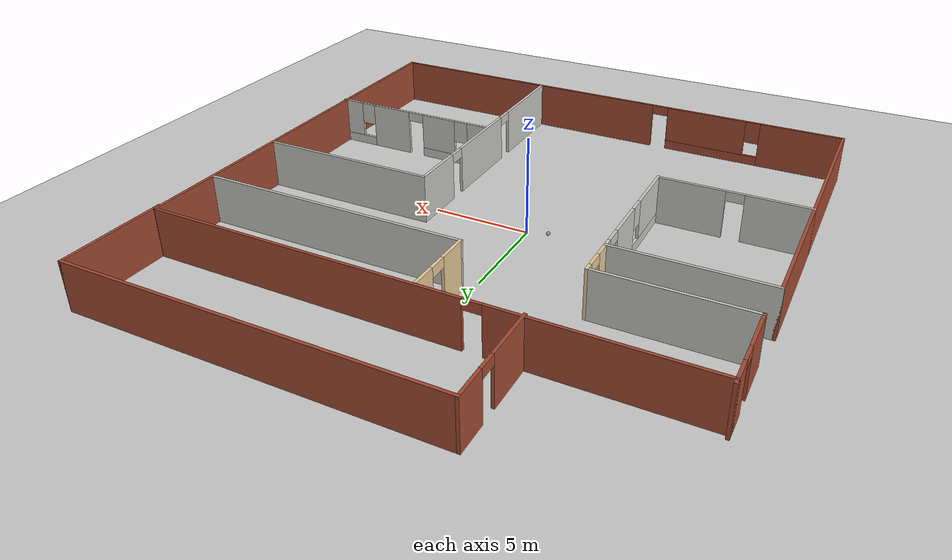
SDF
<sdf version="1.7">
 <world name="default">
  <light name="sun" type="directional">
   <pose>0 0 10 0 -0 0</pose>
   <diffuse>0.8 0.8 0.8 1</diffuse>
   <specular>0.2 0.2 0.2 1</specular>
   <attenuation>
    <range>1000</range>
    <constant>0.9</constant>
    <linear>0.01</linear>
    <quadratic>0.001</quadratic>
   </attenuation>
   <direction>-0.5 0.1 -0.9</direction>
   <spot><inner_angle>0</inner_angle><outer_angle>0</outer_angle><falloff>0</falloff></spot>
  </light>
  <model name="ground_plane">
   <static>1</static>
   <link name="link">
    <collision name="collision">
     <geometry><plane><normal>0 0 1</normal><size>100 100</size></plane></geometry>
     <surface><friction><ode><mu>100</mu><mu2>50</mu2></ode></friction></surface>
    </collision>
    <visual name="visual">
     <cast_shadows>0</cast_shadows>
     <geometry><plane><normal>0 0 1</normal><size>100 100</size></plane></geometry>
     <material>
      <script><uri>file://media/materials/scripts/gazebo.material</uri><name>Gazebo/Grey</name></script>
     </material>
    </visual>
   </link>
  </model>
  <gravity>0 0 -9.8</gravity>
  <magnetic_field>6e-06 2.3e-05 -4.2e-05</magnetic_field>
  <atmosphere type="adiabatic"/>
  <physics type="ode">
   <max_step_size>0.001</max_step_size>
   <real_time_factor>1</real_time_factor>
   <real_time_update_rate>1000</real_time_update_rate>
  </physics>
  <scene><ambient>0.4 0.4 0.4 1</ambient><background>0.7 0.7 0.7 1</background><shadows>1</shadows></scene>
  <spherical_coordinates>
   <surface_model>EARTH_WGS84</surface_model>
   <latitude_deg>0</latitude_deg>
   <longitude_deg>0</longitude_deg>
   <elevation>0</elevation>
   <heading_deg>0</heading_deg>
  </spherical_coordinates>
  <model name="my_ball">
   <link name="link_0">
    <inertial>
     <mass>1</mass>
     <inertia><ixx>0.1</ixx><ixy>0</ixy><ixz>0</ixz><iyy>0.1</iyy><iyz>0</iyz><izz>0.1</izz></inertia>
    </inertial>
    <visual name="visual">
     <geometry><sphere><radius>0.1</radius></sphere></geometry>
     <material>
      <lighting>1</lighting>
      <script><uri>file://media/materials/scripts/gazebo.material</uri><name>Gazebo/Grey</name></script>
      <shader type="pixel"><normal_map>__default__</normal_map></shader>
      <ambient>1 1 1 1</ambient>
      <diffuse>1 1 1 1</diffuse>
      <specular>1 1 1 1</specular>
      <emissive>1 1 1 1</emissive>
     </material>
    </visual>
    <collision name="collision">
     <geometry><sphere><radius>0.1</radius></sphere></geometry>
     <surface>
      <friction>
       <ode><mu>1</mu><mu2>1</mu2><fdir1>0 0 0</fdir1><slip1>0</slip1><slip2>0</slip2></ode>
       <torsional>
        <coefficient>1</coefficient>
        <patch_radius>0</patch_radius>
        <surface_radius>0</surface_radius>
        <use_patch_radius>1</use_patch_radius>
        <ode><slip>0</slip></ode>
       </torsional>
      </friction>
      <bounce><restitution_coefficient>0</restitution_coefficient><threshold>1e+06</threshold></bounce>
      <contact>
       <collide_without_contact>0</collide_without_contact>
       <collide_without_contact_bitmask>1</collide_without_contact_bitmask>
       <collide_bitmask>1</collide_bitmask>
       <ode>
        <soft_cfm>0</soft_cfm>
        <soft_erp>0.2</soft_erp>
        <kp>1e+13</kp>
        <kd>1</kd>
        <max_vel>0.01</max_vel>
        <min_depth>0</min_depth>
       </ode>
       <bullet>
        <split_impulse>1</split_impulse>
        <split_impulse_penetration_threshold>-0.01</split_impulse_penetration_threshold>
        <soft_cfm>0</soft_cfm>
        <soft_erp>0.2</soft_erp>
        <kp>1e+13</kp>
        <kd>1</kd>
       </bullet>
      </contact>
     </surface>
    </collision>
   </link>
   <static>0</static>
   <pose>-1.29169 0.413741 0.5 0 -0 0</pose>
  </model>
  <model name="newworld">
   <link name="Wall_37">
    <pose>-13.3996 -5.55678 0 0 0 -1.5708</pose>
    <visual name="Wall_37_Visual">
     <pose>0 0 1.25 0 -0 0</pose>
     <geometry><box><size>16 0.15 2.5</size></box></geometry>
     <material>
      <script><uri>file://media/materials/scripts/gazebo.material</uri><name>Gazebo/Bricks</name></script>
      <ambient>1 1 1 1</ambient>
      <shader type="pixel"/>
     </material>
     <meta><layer>0</layer></meta>
    </visual>
    <collision name="Wall_37_Collision">
     <pose>0 0 1.25 0 -0 0</pose>
     <geometry><box><size>16 0.15 2.5</size></box></geometry>
     <surface>
      <friction>
       <ode><mu>1</mu><mu2>1</mu2><fdir1>0 0 0</fdir1><slip1>0</slip1><slip2>0</slip2></ode>
       <torsional>
        <coefficient>1</coefficient>
        <patch_radius>0</patch_radius>
        <surface_radius>0</surface_radius>
        <use_patch_radius>1</use_patch_radius>
        <ode><slip>0</slip></ode>
       </torsional>
      </friction>
      <bounce><restitution_coefficient>0</restitution_coefficient><threshold>1e+06</threshold></bounce>
      <contact>
       <collide_without_contact>0</collide_without_contact>
       <collide_without_contact_bitmask>1</collide_without_contact_bitmask>
       <collide_bitmask>1</collide_bitmask>
       <ode>
        <soft_cfm>0</soft_cfm>
        <soft_erp>0.2</soft_erp>
        <kp>1e+13</kp>
        <kd>1</kd>
        <max_vel>0.01</max_vel>
        <min_depth>0</min_depth>
       </ode>
       <bullet>
        <split_impulse>1</split_impulse>
        <split_impulse_penetration_threshold>-0.01</split_impulse_penetration_threshold>
        <soft_cfm>0</soft_cfm>
        <soft_erp>0.2</soft_erp>
        <kp>1e+13</kp>
        <kd>1</kd>
       </bullet>
      </contact>
     </surface>
    </collision>
   </link>
   <link name="Wall_38">
    <pose>-0.039627 -13.5282 0 0 0 -0.003477</pose>
    <visual name="Wall_38_Visual_2">
     <pose>-6.41871 0 0.25 0 -0 0</pose>
     <geometry><box><size>5.24062 0.15 0.5</size></box></geometry>
     <material>
      <script><uri>file://media/materials/scripts/gazebo.material</uri><name>Gazebo/Bricks</name></script>
      <ambient>1 1 1 1</ambient>
      <shader type="pixel"/>
     </material>
     <meta><layer>0</layer></meta>
    </visual>
    <visual name="Wall_38_Visual_4">
     <pose>-8.63902 0 1.9 0 -0 0</pose>
     <geometry><box><size>0.8 0.15 1.2</size></box></geometry>
     <material>
      <script><uri>file://media/materials/scripts/gazebo.material</uri><name>Gazebo/Bricks</name></script>
      <ambient>1 1 1 1</ambient>
      <shader type="pixel"/>
     </material>
     <meta><layer>0</layer></meta>
    </visual>
    <visual name="Wall_38_Visual_0">
     <pose>-11.237 0 1.25 0 -0 0</pose>
     <geometry><box><size>4.39606 0.15 2.5</size></box></geometry>
     <material>
      <script><uri>file://media/materials/scripts/gazebo.material</uri><name>Gazebo/Bricks</name></script>
      <ambient>1 1 1 1</ambient>
      <shader type="pixel"/>
     </material>
     <meta><layer>0</layer></meta>
    </visual>
    <visual name="Wall_38_Visual_1">
     <pose>5.26834 0 1.25 0 -0 0</pose>
     <geometry><box><size>16.3335 0.15 2.5</size></box></geometry>
     <material>
      <script><uri>file://media/materials/scripts/gazebo.material</uri><name>Gazebo/Bricks</name></script>
      <ambient>1 1 1 1</ambient>
      <shader type="pixel"/>
     </material>
     <meta><layer>0</layer></meta>
    </visual>
    <visual name="Wall_38_Visual_3">
     <pose>-6.01871 0 1.5 0 -0 0</pose>
     <geometry><box><size>4.44062 0.15 2</size></box></geometry>
     <material>
      <script><uri>file://media/materials/scripts/gazebo.material</uri><name>Gazebo/Bricks</name></script>
      <ambient>1 1 1 1</ambient>
      <shader type="pixel"/>
     </material>
     <meta><layer>0</layer></meta>
    </visual>
    <visual name="Wall_38_Visual_5">
     <pose>-3.3484 0 2.25 0 -0 0</pose>
     <geometry><box><size>0.9 0.15 0.5</size></box></geometry>
     <material>
      <script><uri>file://media/materials/scripts/gazebo.material</uri><name>Gazebo/Bricks</name></script>
      <ambient>1 1 1 1</ambient>
      <shader type="pixel"/>
     </material>
     <meta><layer>0</layer></meta>
    </visual>
    <collision name="Wall_38_Collision_0">
     <pose>-11.237 0 1.25 0 -0 0</pose>
     <geometry><box><size>4.39606 0.15 2.5</size></box></geometry>
     <surface>
      <friction>
       <ode><mu>1</mu><mu2>1</mu2><fdir1>0 0 0</fdir1><slip1>0</slip1><slip2>0</slip2></ode>
       <torsional>
        <coefficient>1</coefficient>
        <patch_radius>0</patch_radius>
        <surface_radius>0</surface_radius>
        <use_patch_radius>1</use_patch_radius>
        <ode><slip>0</slip></ode>
       </torsional>
      </friction>
      <bounce><restitution_coefficient>0</restitution_coefficient><threshold>1e+06</threshold></bounce>
      <contact>
       <collide_without_contact>0</collide_without_contact>
       <collide_without_contact_bitmask>1</collide_without_contact_bitmask>
       <collide_bitmask>1</collide_bitmask>
       <ode>
        <soft_cfm>0</soft_cfm>
        <soft_erp>0.2</soft_erp>
        <kp>1e+13</kp>
        <kd>1</kd>
        <max_vel>0.01</max_vel>
        <min_depth>0</min_depth>
       </ode>
       <bullet>
        <split_impulse>1</split_impulse>
        <split_impulse_penetration_threshold>-0.01</split_impulse_penetration_threshold>
        <soft_cfm>0</soft_cfm>
        <soft_erp>0.2</soft_erp>
        <kp>1e+13</kp>
        <kd>1</kd>
       </bullet>
      </contact>
     </surface>
    </collision>
    <collision name="Wall_38_Collision_2">
     <pose>-6.41871 0 0.25 0 -0 0</pose>
     <geometry><box><size>5.24062 0.15 0.5</size></box></geometry>
     <surface>
      <friction>
       <ode><mu>1</mu><mu2>1</mu2><fdir1>0 0 0</fdir1><slip1>0</slip1><slip2>0</slip2></ode>
       <torsional>
        <coefficient>1</coefficient>
        <patch_radius>0</patch_radius>
        <surface_radius>0</surface_radius>
        <use_patch_radius>1</use_patch_radius>
        <ode><slip>0</slip></ode>
       </torsional>
      </friction>
      <bounce><restitution_coefficient>0</restitution_coefficient><threshold>1e+06</threshold></bounce>
      <contact>
       <collide_without_contact>0</collide_without_contact>
       <collide_without_contact_bitmask>1</collide_without_contact_bitmask>
       <collide_bitmask>1</collide_bitmask>
       <ode>
        <soft_cfm>0</soft_cfm>
        <soft_erp>0.2</soft_erp>
        <kp>1e+13</kp>
        <kd>1</kd>
        <max_vel>0.01</max_vel>
        <min_depth>0</min_depth>
       </ode>
       <bullet>
        <split_impulse>1</split_impulse>
        <split_impulse_penetration_threshold>-0.01</split_impulse_penetration_threshold>
        <soft_cfm>0</soft_cfm>
        <soft_erp>0.2</soft_erp>
        <kp>1e+13</kp>
        <kd>1</kd>
       </bullet>
      </contact>
     </surface>
    </collision>
    <collision name="Wall_38_Collision_5">
     <pose>-3.3484 0 2.25 0 -0 0</pose>
     <geometry><box><size>0.9 0.15 0.5</size></box></geometry>
     <surface>
      <friction>
       <ode><mu>1</mu><mu2>1</mu2><fdir1>0 0 0</fdir1><slip1>0</slip1><slip2>0</slip2></ode>
       <torsional>
        <coefficient>1</coefficient>
        <patch_radius>0</patch_radius>
        <surface_radius>0</surface_radius>
        <use_patch_radius>1</use_patch_radius>
        <ode><slip>0</slip></ode>
       </torsional>
      </friction>
      <bounce><restitution_coefficient>0</restitution_coefficient><threshold>1e+06</threshold></bounce>
      <contact>
       <collide_without_contact>0</collide_without_contact>
       <collide_without_contact_bitmask>1</collide_without_contact_bitmask>
       <collide_bitmask>1</collide_bitmask>
       <ode>
        <soft_cfm>0</soft_cfm>
        <soft_erp>0.2</soft_erp>
        <kp>1e+13</kp>
        <kd>1</kd>
        <max_vel>0.01</max_vel>
        <min_depth>0</min_depth>
       </ode>
       <bullet>
        <split_impulse>1</split_impulse>
        <split_impulse_penetration_threshold>-0.01</split_impulse_penetration_threshold>
        <soft_cfm>0</soft_cfm>
        <soft_erp>0.2</soft_erp>
        <kp>1e+13</kp>
        <kd>1</kd>
       </bullet>
      </contact>
     </surface>
    </collision>
    <collision name="Wall_38_Collision_4">
     <pose>-8.63902 0 1.9 0 -0 0</pose>
     <geometry><box><size>0.8 0.15 1.2</size></box></geometry>
     <surface>
      <friction>
       <ode><mu>1</mu><mu2>1</mu2><fdir1>0 0 0</fdir1><slip1>0</slip1><slip2>0</slip2></ode>
       <torsional>
        <coefficient>1</coefficient>
        <patch_radius>0</patch_radius>
        <surface_radius>0</surface_radius>
        <use_patch_radius>1</use_patch_radius>
        <ode><slip>0</slip></ode>
       </torsional>
      </friction>
      <bounce><restitution_coefficient>0</restitution_coefficient><threshold>1e+06</threshold></bounce>
      <contact>
       <collide_without_contact>0</collide_without_contact>
       <collide_without_contact_bitmask>1</collide_without_contact_bitmask>
       <collide_bitmask>1</collide_bitmask>
       <ode>
        <soft_cfm>0</soft_cfm>
        <soft_erp>0.2</soft_erp>
        <kp>1e+13</kp>
        <kd>1</kd>
        <max_vel>0.01</max_vel>
        <min_depth>0</min_depth>
       </ode>
       <bullet>
        <split_impulse>1</split_impulse>
        <split_impulse_penetration_threshold>-0.01</split_impulse_penetration_threshold>
        <soft_cfm>0</soft_cfm>
        <soft_erp>0.2</soft_erp>
        <kp>1e+13</kp>
        <kd>1</kd>
       </bullet>
      </contact>
     </surface>
    </collision>
    <collision name="Wall_38_Collision_3">
     <pose>-6.01871 0 1.5 0 -0 0</pose>
     <geometry><box><size>4.44062 0.15 2</size></box></geometry>
     <surface>
      <friction>
       <ode><mu>1</mu><mu2>1</mu2><fdir1>0 0 0</fdir1><slip1>0</slip1><slip2>0</slip2></ode>
       <torsional>
        <coefficient>1</coefficient>
        <patch_radius>0</patch_radius>
        <surface_radius>0</surface_radius>
        <use_patch_radius>1</use_patch_radius>
        <ode><slip>0</slip></ode>
       </torsional>
      </friction>
      <bounce><restitution_coefficient>0</restitution_coefficient><threshold>1e+06</threshold></bounce>
      <contact>
       <collide_without_contact>0</collide_without_contact>
       <collide_without_contact_bitmask>1</collide_without_contact_bitmask>
       <collide_bitmask>1</collide_bitmask>
       <ode>
        <soft_cfm>0</soft_cfm>
        <soft_erp>0.2</soft_erp>
        <kp>1e+13</kp>
        <kd>1</kd>
        <max_vel>0.01</max_vel>
        <min_depth>0</min_depth>
       </ode>
       <bullet>
        <split_impulse>1</split_impulse>
        <split_impulse_penetration_threshold>-0.01</split_impulse_penetration_threshold>
        <soft_cfm>0</soft_cfm>
        <soft_erp>0.2</soft_erp>
        <kp>1e+13</kp>
        <kd>1</kd>
       </bullet>
      </contact>
     </surface>
    </collision>
    <collision name="Wall_38_Collision_1">
     <pose>5.26834 0 1.25 0 -0 0</pose>
     <geometry><box><size>16.3335 0.15 2.5</size></box></geometry>
     <surface>
      <friction>
       <ode><mu>1</mu><mu2>1</mu2><fdir1>0 0 0</fdir1><slip1>0</slip1><slip2>0</slip2></ode>
       <torsional>
        <coefficient>1</coefficient>
        <patch_radius>0</patch_radius>
        <surface_radius>0</surface_radius>
        <use_patch_radius>1</use_patch_radius>
        <ode><slip>0</slip></ode>
       </torsional>
      </friction>
      <bounce><restitution_coefficient>0</restitution_coefficient><threshold>1e+06</threshold></bounce>
      <contact>
       <collide_without_contact>0</collide_without_contact>
       <collide_without_contact_bitmask>1</collide_without_contact_bitmask>
       <collide_bitmask>1</collide_bitmask>
       <ode>
        <soft_cfm>0</soft_cfm>
        <soft_erp>0.2</soft_erp>
        <kp>1e+13</kp>
        <kd>1</kd>
        <max_vel>0.01</max_vel>
        <min_depth>0</min_depth>
       </ode>
       <bullet>
        <split_impulse>1</split_impulse>
        <split_impulse_penetration_threshold>-0.01</split_impulse_penetration_threshold>
        <soft_cfm>0</soft_cfm>
        <soft_erp>0.2</soft_erp>
        <kp>1e+13</kp>
        <kd>1</kd>
       </bullet>
      </contact>
     </surface>
    </collision>
   </link>
   <link name="Wall_39">
    <pose>13.3204 -2.52468 0 0 -0 1.5708</pose>
    <visual name="Wall_39_Visual">
     <pose>0 0 1.25 0 -0 0</pose>
     <geometry><box><size>22.25 0.15 2.5</size></box></geometry>
     <material>
      <script><uri>file://media/materials/scripts/gazebo.material</uri><name>Gazebo/Bricks</name></script>
      <ambient>1 1 1 1</ambient>
      <shader type="pixel"/>
     </material>
     <meta><layer>0</layer></meta>
    </visual>
    <collision name="Wall_39_Collision">
     <pose>0 0 1.25 0 -0 0</pose>
     <geometry><box><size>22.25 0.15 2.5</size></box></geometry>
     <surface>
      <friction>
       <ode><mu>1</mu><mu2>1</mu2><fdir1>0 0 0</fdir1><slip1>0</slip1><slip2>0</slip2></ode>
       <torsional>
        <coefficient>1</coefficient>
        <patch_radius>0</patch_radius>
        <surface_radius>0</surface_radius>
        <use_patch_radius>1</use_patch_radius>
        <ode><slip>0</slip></ode>
       </torsional>
      </friction>
      <bounce><restitution_coefficient>0</restitution_coefficient><threshold>1e+06</threshold></bounce>
      <contact>
       <collide_without_contact>0</collide_without_contact>
       <collide_without_contact_bitmask>1</collide_without_contact_bitmask>
       <collide_bitmask>1</collide_bitmask>
       <ode>
        <soft_cfm>0</soft_cfm>
        <soft_erp>0.2</soft_erp>
        <kp>1e+13</kp>
        <kd>1</kd>
        <max_vel>0.01</max_vel>
        <min_depth>0</min_depth>
       </ode>
       <bullet>
        <split_impulse>1</split_impulse>
        <split_impulse_penetration_threshold>-0.01</split_impulse_penetration_threshold>
        <soft_cfm>0</soft_cfm>
        <soft_erp>0.2</soft_erp>
        <kp>1e+13</kp>
        <kd>1</kd>
       </bullet>
      </contact>
     </surface>
    </collision>
   </link>
   <link name="Wall_40">
    <pose>0.085373 8.57177 0 0 -0 3.13808</pose>
    <visual name="Wall_40_Visual_2">
     <pose>3.09238 0 2.25 0 -0 0</pose>
     <geometry><box><size>0.9 0.15 0.5</size></box></geometry>
     <material>
      <script><uri>file://media/materials/scripts/gazebo.material</uri><name>Gazebo/Bricks</name></script>
      <ambient>1 1 1 1</ambient>
      <shader type="pixel"/>
     </material>
     <meta><layer>0</layer></meta>
    </visual>
    <visual name="Wall_40_Visual_0">
     <pose>-5.33385 0 1.25 0 -0 0</pose>
     <geometry><box><size>15.9525 0.15 2.5</size></box></geometry>
     <material>
      <script><uri>file://media/materials/scripts/gazebo.material</uri><name>Gazebo/Bricks</name></script>
      <ambient>1 1 1 1</ambient>
      <shader type="pixel"/>
     </material>
     <meta><layer>0</layer></meta>
    </visual>
    <visual name="Wall_40_Visual_1">
     <pose>8.42623 0 1.25 0 -0 0</pose>
     <geometry><box><size>9.76771 0.15 2.5</size></box></geometry>
     <material>
      <script><uri>file://media/materials/scripts/gazebo.material</uri><name>Gazebo/Bricks</name></script>
      <ambient>1 1 1 1</ambient>
      <shader type="pixel"/>
     </material>
     <meta><layer>0</layer></meta>
    </visual>
    <collision name="Wall_40_Collision_0">
     <pose>-5.33385 0 1.25 0 -0 0</pose>
     <geometry><box><size>15.9525 0.15 2.5</size></box></geometry>
     <surface>
      <friction>
       <ode><mu>1</mu><mu2>1</mu2><fdir1>0 0 0</fdir1><slip1>0</slip1><slip2>0</slip2></ode>
       <torsional>
        <coefficient>1</coefficient>
        <patch_radius>0</patch_radius>
        <surface_radius>0</surface_radius>
        <use_patch_radius>1</use_patch_radius>
        <ode><slip>0</slip></ode>
       </torsional>
      </friction>
      <bounce><restitution_coefficient>0</restitution_coefficient><threshold>1e+06</threshold></bounce>
      <contact>
       <collide_without_contact>0</collide_without_contact>
       <collide_without_contact_bitmask>1</collide_without_contact_bitmask>
       <collide_bitmask>1</collide_bitmask>
       <ode>
        <soft_cfm>0</soft_cfm>
        <soft_erp>0.2</soft_erp>
        <kp>1e+13</kp>
        <kd>1</kd>
        <max_vel>0.01</max_vel>
        <min_depth>0</min_depth>
       </ode>
       <bullet>
        <split_impulse>1</split_impulse>
        <split_impulse_penetration_threshold>-0.01</split_impulse_penetration_threshold>
        <soft_cfm>0</soft_cfm>
        <soft_erp>0.2</soft_erp>
        <kp>1e+13</kp>
        <kd>1</kd>
       </bullet>
      </contact>
     </surface>
    </collision>
    <collision name="Wall_40_Collision_1">
     <pose>8.42623 0 1.25 0 -0 0</pose>
     <geometry><box><size>9.76771 0.15 2.5</size></box></geometry>
     <surface>
      <friction>
       <ode><mu>1</mu><mu2>1</mu2><fdir1>0 0 0</fdir1><slip1>0</slip1><slip2>0</slip2></ode>
       <torsional>
        <coefficient>1</coefficient>
        <patch_radius>0</patch_radius>
        <surface_radius>0</surface_radius>
        <use_patch_radius>1</use_patch_radius>
        <ode><slip>0</slip></ode>
       </torsional>
      </friction>
      <bounce><restitution_coefficient>0</restitution_coefficient><threshold>1e+06</threshold></bounce>
      <contact>
       <collide_without_contact>0</collide_without_contact>
       <collide_without_contact_bitmask>1</collide_without_contact_bitmask>
       <collide_bitmask>1</collide_bitmask>
       <ode>
        <soft_cfm>0</soft_cfm>
        <soft_erp>0.2</soft_erp>
        <kp>1e+13</kp>
        <kd>1</kd>
        <max_vel>0.01</max_vel>
        <min_depth>0</min_depth>
       </ode>
       <bullet>
        <split_impulse>1</split_impulse>
        <split_impulse_penetration_threshold>-0.01</split_impulse_penetration_threshold>
        <soft_cfm>0</soft_cfm>
        <soft_erp>0.2</soft_erp>
        <kp>1e+13</kp>
        <kd>1</kd>
       </bullet>
      </contact>
     </surface>
    </collision>
    <collision name="Wall_40_Collision_2">
     <pose>3.09238 0 2.25 0 -0 0</pose>
     <geometry><box><size>0.9 0.15 0.5</size></box></geometry>
     <surface>
      <friction>
       <ode><mu>1</mu><mu2>1</mu2><fdir1>0 0 0</fdir1><slip1>0</slip1><slip2>0</slip2></ode>
       <torsional>
        <coefficient>1</coefficient>
        <patch_radius>0</patch_radius>
        <surface_radius>0</surface_radius>
        <use_patch_radius>1</use_patch_radius>
        <ode><slip>0</slip></ode>
       </torsional>
      </friction>
      <bounce><restitution_coefficient>0</restitution_coefficient><threshold>1e+06</threshold></bounce>
      <contact>
       <collide_without_contact>0</collide_without_contact>
       <collide_without_contact_bitmask>1</collide_without_contact_bitmask>
       <collide_bitmask>1</collide_bitmask>
       <ode>
        <soft_cfm>0</soft_cfm>
        <soft_erp>0.2</soft_erp>
        <kp>1e+13</kp>
        <kd>1</kd>
        <max_vel>0.01</max_vel>
        <min_depth>0</min_depth>
       </ode>
       <bullet>
        <split_impulse>1</split_impulse>
        <split_impulse_penetration_threshold>-0.01</split_impulse_penetration_threshold>
        <soft_cfm>0</soft_cfm>
        <soft_erp>0.2</soft_erp>
        <kp>1e+13</kp>
        <kd>1</kd>
       </bullet>
      </contact>
     </surface>
    </collision>
   </link>
   <link name="Wall_43">
    <pose>-9.72463 2.36822 0 0 -0 0</pose>
    <visual name="Wall_43_Visual">
     <pose>0 0 1.25 0 -0 0</pose>
     <geometry><box><size>7.5 0.15 2.5</size></box></geometry>
     <material>
      <script><uri>file://media/materials/scripts/gazebo.material</uri><name>Gazebo/CeilingTiled</name></script>
      <ambient>0.996078 0.47451 0.0196078 1</ambient>
      <shader type="pixel"/>
     </material>
     <meta><layer>0</layer></meta>
    </visual>
    <collision name="Wall_43_Collision">
     <pose>0 0 1.25 0 -0 0</pose>
     <geometry><box><size>7.5 0.15 2.5</size></box></geometry>
     <surface>
      <friction>
       <ode><mu>1</mu><mu2>1</mu2><fdir1>0 0 0</fdir1><slip1>0</slip1><slip2>0</slip2></ode>
       <torsional>
        <coefficient>1</coefficient>
        <patch_radius>0</patch_radius>
        <surface_radius>0</surface_radius>
        <use_patch_radius>1</use_patch_radius>
        <ode><slip>0</slip></ode>
       </torsional>
      </friction>
      <bounce><restitution_coefficient>0</restitution_coefficient><threshold>1e+06</threshold></bounce>
      <contact>
       <collide_without_contact>0</collide_without_contact>
       <collide_without_contact_bitmask>1</collide_without_contact_bitmask>
       <collide_bitmask>1</collide_bitmask>
       <ode>
        <soft_cfm>0</soft_cfm>
        <soft_erp>0.2</soft_erp>
        <kp>1e+13</kp>
        <kd>1</kd>
        <max_vel>0.01</max_vel>
        <min_depth>0</min_depth>
       </ode>
       <bullet>
        <split_impulse>1</split_impulse>
        <split_impulse_penetration_threshold>-0.01</split_impulse_penetration_threshold>
        <soft_cfm>0</soft_cfm>
        <soft_erp>0.2</soft_erp>
        <kp>1e+13</kp>
        <kd>1</kd>
       </bullet>
      </contact>
     </surface>
    </collision>
   </link>
   <link name="Wall_44">
    <pose>-6.04963 3.41822 0 0 -0 1.5708</pose>
    <visual name="Wall_44_Visual_0">
     <pose>-0.670296 0 1.25 0 -0 0</pose>
     <geometry><box><size>0.909407 0.15 2.5</size></box></geometry>
     <material>
      <script><uri>file://media/materials/scripts/gazebo.material</uri><name>Gazebo/Grey</name></script>
      <ambient>0.921569 0.807843 0.615686 1</ambient>
      <shader type="pixel"/>
     </material>
     <meta><layer>0</layer></meta>
    </visual>
    <visual name="Wall_44_Visual_1">
     <pose>0.904704 0 1.25 0 -0 0</pose>
     <geometry><box><size>0.440593 0.15 2.5</size></box></geometry>
     <material>
      <script><uri>file://media/materials/scripts/gazebo.material</uri><name>Gazebo/Grey</name></script>
      <ambient>0.921569 0.807843 0.615686 1</ambient>
      <shader type="pixel"/>
     </material>
     <meta><layer>0</layer></meta>
    </visual>
    <visual name="Wall_44_Visual_2">
     <pose>0.234407 0 2.25 0 -0 0</pose>
     <geometry><box><size>0.9 0.15 0.5</size></box></geometry>
     <material>
      <script><uri>file://media/materials/scripts/gazebo.material</uri><name>Gazebo/Grey</name></script>
      <ambient>0.921569 0.807843 0.615686 1</ambient>
      <shader type="pixel"/>
     </material>
     <meta><layer>0</layer></meta>
    </visual>
    <collision name="Wall_44_Collision_0">
     <pose>-0.670296 0 1.25 0 -0 0</pose>
     <geometry><box><size>0.909407 0.15 2.5</size></box></geometry>
     <surface>
      <friction>
       <ode><mu>1</mu><mu2>1</mu2><fdir1>0 0 0</fdir1><slip1>0</slip1><slip2>0</slip2></ode>
       <torsional>
        <coefficient>1</coefficient>
        <patch_radius>0</patch_radius>
        <surface_radius>0</surface_radius>
        <use_patch_radius>1</use_patch_radius>
        <ode><slip>0</slip></ode>
       </torsional>
      </friction>
      <bounce><restitution_coefficient>0</restitution_coefficient><threshold>1e+06</threshold></bounce>
      <contact>
       <collide_without_contact>0</collide_without_contact>
       <collide_without_contact_bitmask>1</collide_without_contact_bitmask>
       <collide_bitmask>1</collide_bitmask>
       <ode>
        <soft_cfm>0</soft_cfm>
        <soft_erp>0.2</soft_erp>
        <kp>1e+13</kp>
        <kd>1</kd>
        <max_vel>0.01</max_vel>
        <min_depth>0</min_depth>
       </ode>
       <bullet>
        <split_impulse>1</split_impulse>
        <split_impulse_penetration_threshold>-0.01</split_impulse_penetration_threshold>
        <soft_cfm>0</soft_cfm>
        <soft_erp>0.2</soft_erp>
        <kp>1e+13</kp>
        <kd>1</kd>
       </bullet>
      </contact>
     </surface>
    </collision>
    <collision name="Wall_44_Collision_2">
     <pose>0.234407 0 2.25 0 -0 0</pose>
     <geometry><box><size>0.9 0.15 0.5</size></box></geometry>
     <surface>
      <friction>
       <ode><mu>1</mu><mu2>1</mu2><fdir1>0 0 0</fdir1><slip1>0</slip1><slip2>0</slip2></ode>
       <torsional>
        <coefficient>1</coefficient>
        <patch_radius>0</patch_radius>
        <surface_radius>0</surface_radius>
        <use_patch_radius>1</use_patch_radius>
        <ode><slip>0</slip></ode>
       </torsional>
      </friction>
      <bounce><restitution_coefficient>0</restitution_coefficient><threshold>1e+06</threshold></bounce>
      <contact>
       <collide_without_contact>0</collide_without_contact>
       <collide_without_contact_bitmask>1</collide_without_contact_bitmask>
       <collide_bitmask>1</collide_bitmask>
       <ode>
        <soft_cfm>0</soft_cfm>
        <soft_erp>0.2</soft_erp>
        <kp>1e+13</kp>
        <kd>1</kd>
        <max_vel>0.01</max_vel>
        <min_depth>0</min_depth>
       </ode>
       <bullet>
        <split_impulse>1</split_impulse>
        <split_impulse_penetration_threshold>-0.01</split_impulse_penetration_threshold>
        <soft_cfm>0</soft_cfm>
        <soft_erp>0.2</soft_erp>
        <kp>1e+13</kp>
        <kd>1</kd>
       </bullet>
      </contact>
     </surface>
    </collision>
    <collision name="Wall_44_Collision_1">
     <pose>0.904704 0 1.25 0 -0 0</pose>
     <geometry><box><size>0.440593 0.15 2.5</size></box></geometry>
     <surface>
      <friction>
       <ode><mu>1</mu><mu2>1</mu2><fdir1>0 0 0</fdir1><slip1>0</slip1><slip2>0</slip2></ode>
       <torsional>
        <coefficient>1</coefficient>
        <patch_radius>0</patch_radius>
        <surface_radius>0</surface_radius>
        <use_patch_radius>1</use_patch_radius>
        <ode><slip>0</slip></ode>
       </torsional>
      </friction>
      <bounce><restitution_coefficient>0</restitution_coefficient><threshold>1e+06</threshold></bounce>
      <contact>
       <collide_without_contact>0</collide_without_contact>
       <collide_without_contact_bitmask>1</collide_without_contact_bitmask>
       <collide_bitmask>1</collide_bitmask>
       <ode>
        <soft_cfm>0</soft_cfm>
        <soft_erp>0.2</soft_erp>
        <kp>1e+13</kp>
        <kd>1</kd>
        <max_vel>0.01</max_vel>
        <min_depth>0</min_depth>
       </ode>
       <bullet>
        <split_impulse>1</split_impulse>
        <split_impulse_penetration_threshold>-0.01</split_impulse_penetration_threshold>
        <soft_cfm>0</soft_cfm>
        <soft_erp>0.2</soft_erp>
        <kp>1e+13</kp>
        <kd>1</kd>
       </bullet>
      </contact>
     </surface>
    </collision>
   </link>
   <link name="Wall_45">
    <pose>-9.59963 4.46822 0 0 -0 3.14159</pose>
    <visual name="Wall_45_Visual">
     <pose>0 0 1.25 0 -0 0</pose>
     <geometry><box><size>7.25 0.15 2.5</size></box></geometry>
     <material>
      <script><uri>file://media/materials/scripts/gazebo.material</uri><name>Gazebo/CeilingTiled</name></script>
      <ambient>0.921569 0.807843 0.615686 1</ambient>
      <shader type="pixel"/>
     </material>
     <meta><layer>0</layer></meta>
    </visual>
    <collision name="Wall_45_Collision">
     <pose>0 0 1.25 0 -0 0</pose>
     <geometry><box><size>7.25 0.15 2.5</size></box></geometry>
     <surface>
      <friction>
       <ode><mu>1</mu><mu2>1</mu2><fdir1>0 0 0</fdir1><slip1>0</slip1><slip2>0</slip2></ode>
       <torsional>
        <coefficient>1</coefficient>
        <patch_radius>0</patch_radius>
        <surface_radius>0</surface_radius>
        <use_patch_radius>1</use_patch_radius>
        <ode><slip>0</slip></ode>
       </torsional>
      </friction>
      <bounce><restitution_coefficient>0</restitution_coefficient><threshold>1e+06</threshold></bounce>
      <contact>
       <collide_without_contact>0</collide_without_contact>
       <collide_without_contact_bitmask>1</collide_without_contact_bitmask>
       <collide_bitmask>1</collide_bitmask>
       <ode>
        <soft_cfm>0</soft_cfm>
        <soft_erp>0.2</soft_erp>
        <kp>1e+13</kp>
        <kd>1</kd>
        <max_vel>0.01</max_vel>
        <min_depth>0</min_depth>
       </ode>
       <bullet>
        <split_impulse>1</split_impulse>
        <split_impulse_penetration_threshold>-0.01</split_impulse_penetration_threshold>
        <soft_cfm>0</soft_cfm>
        <soft_erp>0.2</soft_erp>
        <kp>1e+13</kp>
        <kd>1</kd>
       </bullet>
      </contact>
     </surface>
    </collision>
   </link>
   <link name="Wall_46">
    <pose>-13.1496 6.64322 0 0 -0 1.5708</pose>
    <visual name="Wall_46_Visual_1">
     <pose>1.54605 0 1.25 0 -0 0</pose>
     <geometry><box><size>1.4079 0.15 2.5</size></box></geometry>
     <material>
      <script><uri>file://media/materials/scripts/gazebo.material</uri><name>Gazebo/Bricks</name></script>
      <ambient>1 1 1 1</ambient>
      <shader type="pixel"/>
     </material>
     <meta><layer>0</layer></meta>
    </visual>
    <visual name="Wall_46_Visual_0">
     <pose>-1.15395 0 1.25 0 -0 0</pose>
     <geometry><box><size>2.1921 0.15 2.5</size></box></geometry>
     <material>
      <script><uri>file://media/materials/scripts/gazebo.material</uri><name>Gazebo/Bricks</name></script>
      <ambient>1 1 1 1</ambient>
      <shader type="pixel"/>
     </material>
     <meta><layer>0</layer></meta>
    </visual>
    <visual name="Wall_46_Visual_2">
     <pose>0.392097 0 2.25 0 -0 0</pose>
     <geometry><box><size>0.9 0.15 0.5</size></box></geometry>
     <material>
      <script><uri>file://media/materials/scripts/gazebo.material</uri><name>Gazebo/Bricks</name></script>
      <ambient>1 1 1 1</ambient>
      <shader type="pixel"/>
     </material>
     <meta><layer>0</layer></meta>
    </visual>
    <collision name="Wall_46_Collision_2">
     <pose>0.392097 0 2.25 0 -0 0</pose>
     <geometry><box><size>0.9 0.15 0.5</size></box></geometry>
     <surface>
      <friction>
       <ode><mu>1</mu><mu2>1</mu2><fdir1>0 0 0</fdir1><slip1>0</slip1><slip2>0</slip2></ode>
       <torsional>
        <coefficient>1</coefficient>
        <patch_radius>0</patch_radius>
        <surface_radius>0</surface_radius>
        <use_patch_radius>1</use_patch_radius>
        <ode><slip>0</slip></ode>
       </torsional>
      </friction>
      <bounce><restitution_coefficient>0</restitution_coefficient><threshold>1e+06</threshold></bounce>
      <contact>
       <collide_without_contact>0</collide_without_contact>
       <collide_without_contact_bitmask>1</collide_without_contact_bitmask>
       <collide_bitmask>1</collide_bitmask>
       <ode>
        <soft_cfm>0</soft_cfm>
        <soft_erp>0.2</soft_erp>
        <kp>1e+13</kp>
        <kd>1</kd>
        <max_vel>0.01</max_vel>
        <min_depth>0</min_depth>
       </ode>
       <bullet>
        <split_impulse>1</split_impulse>
        <split_impulse_penetration_threshold>-0.01</split_impulse_penetration_threshold>
        <soft_cfm>0</soft_cfm>
        <soft_erp>0.2</soft_erp>
        <kp>1e+13</kp>
        <kd>1</kd>
       </bullet>
      </contact>
     </surface>
    </collision>
    <collision name="Wall_46_Collision_0">
     <pose>-1.15395 0 1.25 0 -0 0</pose>
     <geometry><box><size>2.1921 0.15 2.5</size></box></geometry>
     <surface>
      <friction>
       <ode><mu>1</mu><mu2>1</mu2><fdir1>0 0 0</fdir1><slip1>0</slip1><slip2>0</slip2></ode>
       <torsional>
        <coefficient>1</coefficient>
        <patch_radius>0</patch_radius>
        <surface_radius>0</surface_radius>
        <use_patch_radius>1</use_patch_radius>
        <ode><slip>0</slip></ode>
       </torsional>
      </friction>
      <bounce><restitution_coefficient>0</restitution_coefficient><threshold>1e+06</threshold></bounce>
      <contact>
       <collide_without_contact>0</collide_without_contact>
       <collide_without_contact_bitmask>1</collide_without_contact_bitmask>
       <collide_bitmask>1</collide_bitmask>
       <ode>
        <soft_cfm>0</soft_cfm>
        <soft_erp>0.2</soft_erp>
        <kp>1e+13</kp>
        <kd>1</kd>
        <max_vel>0.01</max_vel>
        <min_depth>0</min_depth>
       </ode>
       <bullet>
        <split_impulse>1</split_impulse>
        <split_impulse_penetration_threshold>-0.01</split_impulse_penetration_threshold>
        <soft_cfm>0</soft_cfm>
        <soft_erp>0.2</soft_erp>
        <kp>1e+13</kp>
        <kd>1</kd>
       </bullet>
      </contact>
     </surface>
    </collision>
    <collision name="Wall_46_Collision_1">
     <pose>1.54605 0 1.25 0 -0 0</pose>
     <geometry><box><size>1.4079 0.15 2.5</size></box></geometry>
     <surface>
      <friction>
       <ode><mu>1</mu><mu2>1</mu2><fdir1>0 0 0</fdir1><slip1>0</slip1><slip2>0</slip2></ode>
       <torsional>
        <coefficient>1</coefficient>
        <patch_radius>0</patch_radius>
        <surface_radius>0</surface_radius>
        <use_patch_radius>1</use_patch_radius>
        <ode><slip>0</slip></ode>
       </torsional>
      </friction>
      <bounce><restitution_coefficient>0</restitution_coefficient><threshold>1e+06</threshold></bounce>
      <contact>
       <collide_without_contact>0</collide_without_contact>
       <collide_without_contact_bitmask>1</collide_without_contact_bitmask>
       <collide_bitmask>1</collide_bitmask>
       <ode>
        <soft_cfm>0</soft_cfm>
        <soft_erp>0.2</soft_erp>
        <kp>1e+13</kp>
        <kd>1</kd>
        <max_vel>0.01</max_vel>
        <min_depth>0</min_depth>
       </ode>
       <bullet>
        <split_impulse>1</split_impulse>
        <split_impulse_penetration_threshold>-0.01</split_impulse_penetration_threshold>
        <soft_cfm>0</soft_cfm>
        <soft_erp>0.2</soft_erp>
        <kp>1e+13</kp>
        <kd>1</kd>
       </bullet>
      </contact>
     </surface>
    </collision>
   </link>
   <link name="Wall_48">
    <pose>4.11037 -6.62501 0 0 -0 1.5708</pose>
    <visual name="Wall_48_Visual_1">
     <pose>0.963424 0 1.25 0 -0 0</pose>
     <geometry><box><size>4.57028 0.15 2.5</size></box></geometry>
     <material>
      <script><uri>file://media/materials/scripts/gazebo.material</uri><name>Gazebo/CeilingTiled</name></script>
      <ambient>0.435294 0.796078 0.67451 1</ambient>
      <shader type="pixel"/>
     </material>
     <meta><layer>0</layer></meta>
    </visual>
    <visual name="Wall_48_Visual_3">
     <pose>-1.77172 0 2.25 0 -0 0</pose>
     <geometry><box><size>0.9 0.15 0.5</size></box></geometry>
     <material>
      <script><uri>file://media/materials/scripts/gazebo.material</uri><name>Gazebo/CeilingTiled</name></script>
      <ambient>0.435294 0.796078 0.67451 1</ambient>
      <shader type="pixel"/>
     </material>
     <meta><layer>0</layer></meta>
    </visual>
    <visual name="Wall_48_Visual_4">
     <pose>3.69857 0 2.25 0 -0 0</pose>
     <geometry><box><size>0.9 0.15 0.5</size></box></geometry>
     <material>
      <script><uri>file://media/materials/scripts/gazebo.material</uri><name>Gazebo/CeilingTiled</name></script>
      <ambient>0.435294 0.796078 0.67451 1</ambient>
      <shader type="pixel"/>
     </material>
     <meta><layer>0</layer></meta>
    </visual>
    <visual name="Wall_48_Visual_2">
     <pose>5.57428 0 1.25 0 -0 0</pose>
     <geometry><box><size>2.85143 0.15 2.5</size></box></geometry>
     <material>
      <script><uri>file://media/materials/scripts/gazebo.material</uri><name>Gazebo/CeilingTiled</name></script>
      <ambient>0.435294 0.796078 0.67451 1</ambient>
      <shader type="pixel"/>
     </material>
     <meta><layer>0</layer></meta>
    </visual>
    <visual name="Wall_48_Visual_0">
     <pose>-4.61086 0 1.25 0 -0 0</pose>
     <geometry><box><size>4.77828 0.15 2.5</size></box></geometry>
     <material>
      <script><uri>file://media/materials/scripts/gazebo.material</uri><name>Gazebo/CeilingTiled</name></script>
      <ambient>0.435294 0.796078 0.67451 1</ambient>
      <shader type="pixel"/>
     </material>
     <meta><layer>0</layer></meta>
    </visual>
    <collision name="Wall_48_Collision_2">
     <pose>5.57428 0 1.25 0 -0 0</pose>
     <geometry><box><size>2.85143 0.15 2.5</size></box></geometry>
     <surface>
      <friction>
       <ode><mu>1</mu><mu2>1</mu2><fdir1>0 0 0</fdir1><slip1>0</slip1><slip2>0</slip2></ode>
       <torsional>
        <coefficient>1</coefficient>
        <patch_radius>0</patch_radius>
        <surface_radius>0</surface_radius>
        <use_patch_radius>1</use_patch_radius>
        <ode><slip>0</slip></ode>
       </torsional>
      </friction>
      <bounce><restitution_coefficient>0</restitution_coefficient><threshold>1e+06</threshold></bounce>
      <contact>
       <collide_without_contact>0</collide_without_contact>
       <collide_without_contact_bitmask>1</collide_without_contact_bitmask>
       <collide_bitmask>1</collide_bitmask>
       <ode>
        <soft_cfm>0</soft_cfm>
        <soft_erp>0.2</soft_erp>
        <kp>1e+13</kp>
        <kd>1</kd>
        <max_vel>0.01</max_vel>
        <min_depth>0</min_depth>
       </ode>
       <bullet>
        <split_impulse>1</split_impulse>
        <split_impulse_penetration_threshold>-0.01</split_impulse_penetration_threshold>
        <soft_cfm>0</soft_cfm>
        <soft_erp>0.2</soft_erp>
        <kp>1e+13</kp>
        <kd>1</kd>
       </bullet>
      </contact>
     </surface>
    </collision>
    <collision name="Wall_48_Collision_1">
     <pose>0.963424 0 1.25 0 -0 0</pose>
     <geometry><box><size>4.57028 0.15 2.5</size></box></geometry>
     <surface>
      <friction>
       <ode><mu>1</mu><mu2>1</mu2><fdir1>0 0 0</fdir1><slip1>0</slip1><slip2>0</slip2></ode>
       <torsional>
        <coefficient>1</coefficient>
        <patch_radius>0</patch_radius>
        <surface_radius>0</surface_radius>
        <use_patch_radius>1</use_patch_radius>
        <ode><slip>0</slip></ode>
       </torsional>
      </friction>
      <bounce><restitution_coefficient>0</restitution_coefficient><threshold>1e+06</threshold></bounce>
      <contact>
       <collide_without_contact>0</collide_without_contact>
       <collide_without_contact_bitmask>1</collide_without_contact_bitmask>
       <collide_bitmask>1</collide_bitmask>
       <ode>
        <soft_cfm>0</soft_cfm>
        <soft_erp>0.2</soft_erp>
        <kp>1e+13</kp>
        <kd>1</kd>
        <max_vel>0.01</max_vel>
        <min_depth>0</min_depth>
       </ode>
       <bullet>
        <split_impulse>1</split_impulse>
        <split_impulse_penetration_threshold>-0.01</split_impulse_penetration_threshold>
        <soft_cfm>0</soft_cfm>
        <soft_erp>0.2</soft_erp>
        <kp>1e+13</kp>
        <kd>1</kd>
       </bullet>
      </contact>
     </surface>
    </collision>
    <collision name="Wall_48_Collision_3">
     <pose>-1.77172 0 2.25 0 -0 0</pose>
     <geometry><box><size>0.9 0.15 0.5</size></box></geometry>
     <surface>
      <friction>
       <ode><mu>1</mu><mu2>1</mu2><fdir1>0 0 0</fdir1><slip1>0</slip1><slip2>0</slip2></ode>
       <torsional>
        <coefficient>1</coefficient>
        <patch_radius>0</patch_radius>
        <surface_radius>0</surface_radius>
        <use_patch_radius>1</use_patch_radius>
        <ode><slip>0</slip></ode>
       </torsional>
      </friction>
      <bounce><restitution_coefficient>0</restitution_coefficient><threshold>1e+06</threshold></bounce>
      <contact>
       <collide_without_contact>0</collide_without_contact>
       <collide_without_contact_bitmask>1</collide_without_contact_bitmask>
       <collide_bitmask>1</collide_bitmask>
       <ode>
        <soft_cfm>0</soft_cfm>
        <soft_erp>0.2</soft_erp>
        <kp>1e+13</kp>
        <kd>1</kd>
        <max_vel>0.01</max_vel>
        <min_depth>0</min_depth>
       </ode>
       <bullet>
        <split_impulse>1</split_impulse>
        <split_impulse_penetration_threshold>-0.01</split_impulse_penetration_threshold>
        <soft_cfm>0</soft_cfm>
        <soft_erp>0.2</soft_erp>
        <kp>1e+13</kp>
        <kd>1</kd>
       </bullet>
      </contact>
     </surface>
    </collision>
    <collision name="Wall_48_Collision_0">
     <pose>-4.61086 0 1.25 0 -0 0</pose>
     <geometry><box><size>4.77828 0.15 2.5</size></box></geometry>
     <surface>
      <friction>
       <ode><mu>1</mu><mu2>1</mu2><fdir1>0 0 0</fdir1><slip1>0</slip1><slip2>0</slip2></ode>
       <torsional>
        <coefficient>1</coefficient>
        <patch_radius>0</patch_radius>
        <surface_radius>0</surface_radius>
        <use_patch_radius>1</use_patch_radius>
        <ode><slip>0</slip></ode>
       </torsional>
      </friction>
      <bounce><restitution_coefficient>0</restitution_coefficient><threshold>1e+06</threshold></bounce>
      <contact>
       <collide_without_contact>0</collide_without_contact>
       <collide_without_contact_bitmask>1</collide_without_contact_bitmask>
       <collide_bitmask>1</collide_bitmask>
       <ode>
        <soft_cfm>0</soft_cfm>
        <soft_erp>0.2</soft_erp>
        <kp>1e+13</kp>
        <kd>1</kd>
        <max_vel>0.01</max_vel>
        <min_depth>0</min_depth>
       </ode>
       <bullet>
        <split_impulse>1</split_impulse>
        <split_impulse_penetration_threshold>-0.01</split_impulse_penetration_threshold>
        <soft_cfm>0</soft_cfm>
        <soft_erp>0.2</soft_erp>
        <kp>1e+13</kp>
        <kd>1</kd>
       </bullet>
      </contact>
     </surface>
    </collision>
    <collision name="Wall_48_Collision_4">
     <pose>3.69857 0 2.25 0 -0 0</pose>
     <geometry><box><size>0.9 0.15 0.5</size></box></geometry>
     <surface>
      <friction>
       <ode><mu>1</mu><mu2>1</mu2><fdir1>0 0 0</fdir1><slip1>0</slip1><slip2>0</slip2></ode>
       <torsional>
        <coefficient>1</coefficient>
        <patch_radius>0</patch_radius>
        <surface_radius>0</surface_radius>
        <use_patch_radius>1</use_patch_radius>
        <ode><slip>0</slip></ode>
       </torsional>
      </friction>
      <bounce><restitution_coefficient>0</restitution_coefficient><threshold>1e+06</threshold></bounce>
      <contact>
       <collide_without_contact>0</collide_without_contact>
       <collide_without_contact_bitmask>1</collide_without_contact_bitmask>
       <collide_bitmask>1</collide_bitmask>
       <ode>
        <soft_cfm>0</soft_cfm>
        <soft_erp>0.2</soft_erp>
        <kp>1e+13</kp>
        <kd>1</kd>
        <max_vel>0.01</max_vel>
        <min_depth>0</min_depth>
       </ode>
       <bullet>
        <split_impulse>1</split_impulse>
        <split_impulse_penetration_threshold>-0.01</split_impulse_penetration_threshold>
        <soft_cfm>0</soft_cfm>
        <soft_erp>0.2</soft_erp>
        <kp>1e+13</kp>
        <kd>1</kd>
       </bullet>
      </contact>
     </surface>
    </collision>
   </link>
   <link name="Wall_49">
    <pose>8.66037 0.299991 0 0 -0 0</pose>
    <visual name="Wall_49_Visual">
     <pose>0 0 1.25 0 -0 0</pose>
     <geometry><box><size>9.25 0.15 2.5</size></box></geometry>
     <material>
      <script><uri>file://media/materials/scripts/gazebo.material</uri><name>Gazebo/CeilingTiled</name></script>
      <ambient>0.435294 0.796078 0.67451 1</ambient>
      <shader type="pixel"/>
     </material>
     <meta><layer>0</layer></meta>
    </visual>
    <collision name="Wall_49_Collision">
     <pose>0 0 1.25 0 -0 0</pose>
     <geometry><box><size>9.25 0.15 2.5</size></box></geometry>
     <surface>
      <friction>
       <ode><mu>1</mu><mu2>1</mu2><fdir1>0 0 0</fdir1><slip1>0</slip1><slip2>0</slip2></ode>
       <torsional>
        <coefficient>1</coefficient>
        <patch_radius>0</patch_radius>
        <surface_radius>0</surface_radius>
        <use_patch_radius>1</use_patch_radius>
        <ode><slip>0</slip></ode>
       </torsional>
      </friction>
      <bounce><restitution_coefficient>0</restitution_coefficient><threshold>1e+06</threshold></bounce>
      <contact>
       <collide_without_contact>0</collide_without_contact>
       <collide_without_contact_bitmask>1</collide_without_contact_bitmask>
       <collide_bitmask>1</collide_bitmask>
       <ode>
        <soft_cfm>0</soft_cfm>
        <soft_erp>0.2</soft_erp>
        <kp>1e+13</kp>
        <kd>1</kd>
        <max_vel>0.01</max_vel>
        <min_depth>0</min_depth>
       </ode>
       <bullet>
        <split_impulse>1</split_impulse>
        <split_impulse_penetration_threshold>-0.01</split_impulse_penetration_threshold>
        <soft_cfm>0</soft_cfm>
        <soft_erp>0.2</soft_erp>
        <kp>1e+13</kp>
        <kd>1</kd>
       </bullet>
      </contact>
     </surface>
    </collision>
   </link>
   <link name="Wall_51">
    <pose>8.84288 -6.35816 0 0 -0 0</pose>
    <visual name="Wall_51_Visual_4">
     <pose>-1.69834 0 1.5 0 -0 0</pose>
     <geometry><box><size>2.02335 0.15 2</size></box></geometry>
     <material>
      <script><uri>file://media/materials/scripts/gazebo.material</uri><name>Gazebo/CeilingTiled</name></script>
      <ambient>0.435294 0.796078 0.67451 1</ambient>
      <shader type="pixel"/>
     </material>
     <meta><layer>0</layer></meta>
    </visual>
    <visual name="Wall_51_Visual_5">
     <pose>-1.69834 0 1.5 0 -0 0</pose>
     <geometry><box><size>2.02335 0.15 2</size></box></geometry>
     <material>
      <script><uri>file://media/materials/scripts/gazebo.material</uri><name>Gazebo/CeilingTiled</name></script>
      <ambient>0.435294 0.796078 0.67451 1</ambient>
      <shader type="pixel"/>
     </material>
     <meta><layer>0</layer></meta>
    </visual>
    <visual name="Wall_51_Visual_9">
     <pose>-0.236664 0 2.25 0 -0 0</pose>
     <geometry><box><size>0.9 0.15 0.5</size></box></geometry>
     <material>
      <script><uri>file://media/materials/scripts/gazebo.material</uri><name>Gazebo/CeilingTiled</name></script>
      <ambient>0.435294 0.796078 0.67451 1</ambient>
      <shader type="pixel"/>
     </material>
     <meta><layer>0</layer></meta>
    </visual>
    <visual name="Wall_51_Visual_2">
     <pose>-2.09834 0 0.25 0 -0 0</pose>
     <geometry><box><size>2.82335 0.15 0.5</size></box></geometry>
     <material>
      <script><uri>file://media/materials/scripts/gazebo.material</uri><name>Gazebo/CeilingTiled</name></script>
      <ambient>0.435294 0.796078 0.67451 1</ambient>
      <shader type="pixel"/>
     </material>
     <meta><layer>0</layer></meta>
    </visual>
    <visual name="Wall_51_Visual_1">
     <pose>1.37624 0 1.25 0 -0 0</pose>
     <geometry><box><size>2.3258 0.15 2.5</size></box></geometry>
     <material>
      <script><uri>file://media/materials/scripts/gazebo.material</uri><name>Gazebo/CeilingTiled</name></script>
      <ambient>0.435294 0.796078 0.67451 1</ambient>
      <shader type="pixel"/>
     </material>
     <meta><layer>0</layer></meta>
    </visual>
    <visual name="Wall_51_Visual_10">
     <pose>-0.236664 0 2.25 0 -0 0</pose>
     <geometry><box><size>0.9 0.15 0.5</size></box></geometry>
     <material>
      <script><uri>file://media/materials/scripts/gazebo.material</uri><name>Gazebo/CeilingTiled</name></script>
      <ambient>0.435294 0.796078 0.67451 1</ambient>
      <shader type="pixel"/>
     </material>
     <meta><layer>0</layer></meta>
    </visual>
    <visual name="Wall_51_Visual_3">
     <pose>3.58207 0 0.25 0 -0 0</pose>
     <geometry><box><size>2.08586 0.15 0.5</size></box></geometry>
     <material>
      <script><uri>file://media/materials/scripts/gazebo.material</uri><name>Gazebo/CeilingTiled</name></script>
      <ambient>0.435294 0.796078 0.67451 1</ambient>
      <shader type="pixel"/>
     </material>
     <meta><layer>0</layer></meta>
    </visual>
    <visual name="Wall_51_Visual_8">
     <pose>2.93914 0 1.9 0 -0 0</pose>
     <geometry><box><size>0.8 0.15 1.2</size></box></geometry>
     <material>
      <script><uri>file://media/materials/scripts/gazebo.material</uri><name>Gazebo/CeilingTiled</name></script>
      <ambient>0.435294 0.796078 0.67451 1</ambient>
      <shader type="pixel"/>
     </material>
     <meta><layer>0</layer></meta>
    </visual>
    <visual name="Wall_51_Visual_0">
     <pose>-4.0675 0 1.25 0 -0 0</pose>
     <geometry><box><size>1.11499 0.15 2.5</size></box></geometry>
     <material>
      <script><uri>file://media/materials/scripts/gazebo.material</uri><name>Gazebo/CeilingTiled</name></script>
      <ambient>0.435294 0.796078 0.67451 1</ambient>
      <shader type="pixel"/>
     </material>
     <meta><layer>0</layer></meta>
    </visual>
    <visual name="Wall_51_Visual_7">
     <pose>-3.11001 0 1.9 0 -0 0</pose>
     <geometry><box><size>0.8 0.15 1.2</size></box></geometry>
     <material>
      <script><uri>file://media/materials/scripts/gazebo.material</uri><name>Gazebo/CeilingTiled</name></script>
      <ambient>0.435294 0.796078 0.67451 1</ambient>
      <shader type="pixel"/>
     </material>
     <meta><layer>0</layer></meta>
    </visual>
    <visual name="Wall_51_Visual_6">
     <pose>3.98207 0 1.5 0 -0 0</pose>
     <geometry><box><size>1.28586 0.15 2</size></box></geometry>
     <material>
      <script><uri>file://media/materials/scripts/gazebo.material</uri><name>Gazebo/CeilingTiled</name></script>
      <ambient>0.435294 0.796078 0.67451 1</ambient>
      <shader type="pixel"/>
     </material>
     <meta><layer>0</layer></meta>
    </visual>
    <collision name="Wall_51_Collision_6">
     <pose>3.98207 0 1.5 0 -0 0</pose>
     <geometry><box><size>1.28586 0.15 2</size></box></geometry>
     <surface>
      <friction>
       <ode><mu>1</mu><mu2>1</mu2><fdir1>0 0 0</fdir1><slip1>0</slip1><slip2>0</slip2></ode>
       <torsional>
        <coefficient>1</coefficient>
        <patch_radius>0</patch_radius>
        <surface_radius>0</surface_radius>
        <use_patch_radius>1</use_patch_radius>
        <ode><slip>0</slip></ode>
       </torsional>
      </friction>
      <bounce><restitution_coefficient>0</restitution_coefficient><threshold>1e+06</threshold></bounce>
      <contact>
       <collide_without_contact>0</collide_without_contact>
       <collide_without_contact_bitmask>1</collide_without_contact_bitmask>
       <collide_bitmask>1</collide_bitmask>
       <ode>
        <soft_cfm>0</soft_cfm>
        <soft_erp>0.2</soft_erp>
        <kp>1e+13</kp>
        <kd>1</kd>
        <max_vel>0.01</max_vel>
        <min_depth>0</min_depth>
       </ode>
       <bullet>
        <split_impulse>1</split_impulse>
        <split_impulse_penetration_threshold>-0.01</split_impulse_penetration_threshold>
        <soft_cfm>0</soft_cfm>
        <soft_erp>0.2</soft_erp>
        <kp>1e+13</kp>
        <kd>1</kd>
       </bullet>
      </contact>
     </surface>
    </collision>
    <collision name="Wall_51_Collision_10">
     <pose>-0.236664 0 2.25 0 -0 0</pose>
     <geometry><box><size>0.9 0.15 0.5</size></box></geometry>
     <surface>
      <friction>
       <ode><mu>1</mu><mu2>1</mu2><fdir1>0 0 0</fdir1><slip1>0</slip1><slip2>0</slip2></ode>
       <torsional>
        <coefficient>1</coefficient>
        <patch_radius>0</patch_radius>
        <surface_radius>0</surface_radius>
        <use_patch_radius>1</use_patch_radius>
        <ode><slip>0</slip></ode>
       </torsional>
      </friction>
      <bounce><restitution_coefficient>0</restitution_coefficient><threshold>1e+06</threshold></bounce>
      <contact>
       <collide_without_contact>0</collide_without_contact>
       <collide_without_contact_bitmask>1</collide_without_contact_bitmask>
       <collide_bitmask>1</collide_bitmask>
       <ode>
        <soft_cfm>0</soft_cfm>
        <soft_erp>0.2</soft_erp>
        <kp>1e+13</kp>
        <kd>1</kd>
        <max_vel>0.01</max_vel>
        <min_depth>0</min_depth>
       </ode>
       <bullet>
        <split_impulse>1</split_impulse>
        <split_impulse_penetration_threshold>-0.01</split_impulse_penetration_threshold>
        <soft_cfm>0</soft_cfm>
        <soft_erp>0.2</soft_erp>
        <kp>1e+13</kp>
        <kd>1</kd>
       </bullet>
      </contact>
     </surface>
    </collision>
    <collision name="Wall_51_Collision_9">
     <pose>-0.236664 0 2.25 0 -0 0</pose>
     <geometry><box><size>0.9 0.15 0.5</size></box></geometry>
     <surface>
      <friction>
       <ode><mu>1</mu><mu2>1</mu2><fdir1>0 0 0</fdir1><slip1>0</slip1><slip2>0</slip2></ode>
       <torsional>
        <coefficient>1</coefficient>
        <patch_radius>0</patch_radius>
        <surface_radius>0</surface_radius>
        <use_patch_radius>1</use_patch_radius>
        <ode><slip>0</slip></ode>
       </torsional>
      </friction>
      <bounce><restitution_coefficient>0</restitution_coefficient><threshold>1e+06</threshold></bounce>
      <contact>
       <collide_without_contact>0</collide_without_contact>
       <collide_without_contact_bitmask>1</collide_without_contact_bitmask>
       <collide_bitmask>1</collide_bitmask>
       <ode>
        <soft_cfm>0</soft_cfm>
        <soft_erp>0.2</soft_erp>
        <kp>1e+13</kp>
        <kd>1</kd>
        <max_vel>0.01</max_vel>
        <min_depth>0</min_depth>
       </ode>
       <bullet>
        <split_impulse>1</split_impulse>
        <split_impulse_penetration_threshold>-0.01</split_impulse_penetration_threshold>
        <soft_cfm>0</soft_cfm>
        <soft_erp>0.2</soft_erp>
        <kp>1e+13</kp>
        <kd>1</kd>
       </bullet>
      </contact>
     </surface>
    </collision>
    <collision name="Wall_51_Collision_5">
     <pose>-1.69834 0 1.5 0 -0 0</pose>
     <geometry><box><size>2.02335 0.15 2</size></box></geometry>
     <surface>
      <friction>
       <ode><mu>1</mu><mu2>1</mu2><fdir1>0 0 0</fdir1><slip1>0</slip1><slip2>0</slip2></ode>
       <torsional>
        <coefficient>1</coefficient>
        <patch_radius>0</patch_radius>
        <surface_radius>0</surface_radius>
        <use_patch_radius>1</use_patch_radius>
        <ode><slip>0</slip></ode>
       </torsional>
      </friction>
      <bounce><restitution_coefficient>0</restitution_coefficient><threshold>1e+06</threshold></bounce>
      <contact>
       <collide_without_contact>0</collide_without_contact>
       <collide_without_contact_bitmask>1</collide_without_contact_bitmask>
       <collide_bitmask>1</collide_bitmask>
       <ode>
        <soft_cfm>0</soft_cfm>
        <soft_erp>0.2</soft_erp>
        <kp>1e+13</kp>
        <kd>1</kd>
        <max_vel>0.01</max_vel>
        <min_depth>0</min_depth>
       </ode>
       <bullet>
        <split_impulse>1</split_impulse>
        <split_impulse_penetration_threshold>-0.01</split_impulse_penetration_threshold>
        <soft_cfm>0</soft_cfm>
        <soft_erp>0.2</soft_erp>
        <kp>1e+13</kp>
        <kd>1</kd>
       </bullet>
      </contact>
     </surface>
    </collision>
    <collision name="Wall_51_Collision_8">
     <pose>2.93914 0 1.9 0 -0 0</pose>
     <geometry><box><size>0.8 0.15 1.2</size></box></geometry>
     <surface>
      <friction>
       <ode><mu>1</mu><mu2>1</mu2><fdir1>0 0 0</fdir1><slip1>0</slip1><slip2>0</slip2></ode>
       <torsional>
        <coefficient>1</coefficient>
        <patch_radius>0</patch_radius>
        <surface_radius>0</surface_radius>
        <use_patch_radius>1</use_patch_radius>
        <ode><slip>0</slip></ode>
       </torsional>
      </friction>
      <bounce><restitution_coefficient>0</restitution_coefficient><threshold>1e+06</threshold></bounce>
      <contact>
       <collide_without_contact>0</collide_without_contact>
       <collide_without_contact_bitmask>1</collide_without_contact_bitmask>
       <collide_bitmask>1</collide_bitmask>
       <ode>
        <soft_cfm>0</soft_cfm>
        <soft_erp>0.2</soft_erp>
        <kp>1e+13</kp>
        <kd>1</kd>
        <max_vel>0.01</max_vel>
        <min_depth>0</min_depth>
       </ode>
       <bullet>
        <split_impulse>1</split_impulse>
        <split_impulse_penetration_threshold>-0.01</split_impulse_penetration_threshold>
        <soft_cfm>0</soft_cfm>
        <soft_erp>0.2</soft_erp>
        <kp>1e+13</kp>
        <kd>1</kd>
       </bullet>
      </contact>
     </surface>
    </collision>
    <collision name="Wall_51_Collision_0">
     <pose>-4.0675 0 1.25 0 -0 0</pose>
     <geometry><box><size>1.11499 0.15 2.5</size></box></geometry>
     <surface>
      <friction>
       <ode><mu>1</mu><mu2>1</mu2><fdir1>0 0 0</fdir1><slip1>0</slip1><slip2>0</slip2></ode>
       <torsional>
        <coefficient>1</coefficient>
        <patch_radius>0</patch_radius>
        <surface_radius>0</surface_radius>
        <use_patch_radius>1</use_patch_radius>
        <ode><slip>0</slip></ode>
       </torsional>
      </friction>
      <bounce><restitution_coefficient>0</restitution_coefficient><threshold>1e+06</threshold></bounce>
      <contact>
       <collide_without_contact>0</collide_without_contact>
       <collide_without_contact_bitmask>1</collide_without_contact_bitmask>
       <collide_bitmask>1</collide_bitmask>
       <ode>
        <soft_cfm>0</soft_cfm>
        <soft_erp>0.2</soft_erp>
        <kp>1e+13</kp>
        <kd>1</kd>
        <max_vel>0.01</max_vel>
        <min_depth>0</min_depth>
       </ode>
       <bullet>
        <split_impulse>1</split_impulse>
        <split_impulse_penetration_threshold>-0.01</split_impulse_penetration_threshold>
        <soft_cfm>0</soft_cfm>
        <soft_erp>0.2</soft_erp>
        <kp>1e+13</kp>
        <kd>1</kd>
       </bullet>
      </contact>
     </surface>
    </collision>
    <collision name="Wall_51_Collision_3">
     <pose>3.58207 0 0.25 0 -0 0</pose>
     <geometry><box><size>2.08586 0.15 0.5</size></box></geometry>
     <surface>
      <friction>
       <ode><mu>1</mu><mu2>1</mu2><fdir1>0 0 0</fdir1><slip1>0</slip1><slip2>0</slip2></ode>
       <torsional>
        <coefficient>1</coefficient>
        <patch_radius>0</patch_radius>
        <surface_radius>0</surface_radius>
        <use_patch_radius>1</use_patch_radius>
        <ode><slip>0</slip></ode>
       </torsional>
      </friction>
      <bounce><restitution_coefficient>0</restitution_coefficient><threshold>1e+06</threshold></bounce>
      <contact>
       <collide_without_contact>0</collide_without_contact>
       <collide_without_contact_bitmask>1</collide_without_contact_bitmask>
       <collide_bitmask>1</collide_bitmask>
       <ode>
        <soft_cfm>0</soft_cfm>
        <soft_erp>0.2</soft_erp>
        <kp>1e+13</kp>
        <kd>1</kd>
        <max_vel>0.01</max_vel>
        <min_depth>0</min_depth>
       </ode>
       <bullet>
        <split_impulse>1</split_impulse>
        <split_impulse_penetration_threshold>-0.01</split_impulse_penetration_threshold>
        <soft_cfm>0</soft_cfm>
        <soft_erp>0.2</soft_erp>
        <kp>1e+13</kp>
        <kd>1</kd>
       </bullet>
      </contact>
     </surface>
    </collision>
    <collision name="Wall_51_Collision_4">
     <pose>-1.69834 0 1.5 0 -0 0</pose>
     <geometry><box><size>2.02335 0.15 2</size></box></geometry>
     <surface>
      <friction>
       <ode><mu>1</mu><mu2>1</mu2><fdir1>0 0 0</fdir1><slip1>0</slip1><slip2>0</slip2></ode>
       <torsional>
        <coefficient>1</coefficient>
        <patch_radius>0</patch_radius>
        <surface_radius>0</surface_radius>
        <use_patch_radius>1</use_patch_radius>
        <ode><slip>0</slip></ode>
       </torsional>
      </friction>
      <bounce><restitution_coefficient>0</restitution_coefficient><threshold>1e+06</threshold></bounce>
      <contact>
       <collide_without_contact>0</collide_without_contact>
       <collide_without_contact_bitmask>1</collide_without_contact_bitmask>
       <collide_bitmask>1</collide_bitmask>
       <ode>
        <soft_cfm>0</soft_cfm>
        <soft_erp>0.2</soft_erp>
        <kp>1e+13</kp>
        <kd>1</kd>
        <max_vel>0.01</max_vel>
        <min_depth>0</min_depth>
       </ode>
       <bullet>
        <split_impulse>1</split_impulse>
        <split_impulse_penetration_threshold>-0.01</split_impulse_penetration_threshold>
        <soft_cfm>0</soft_cfm>
        <soft_erp>0.2</soft_erp>
        <kp>1e+13</kp>
        <kd>1</kd>
       </bullet>
      </contact>
     </surface>
    </collision>
    <collision name="Wall_51_Collision_7">
     <pose>-3.11001 0 1.9 0 -0 0</pose>
     <geometry><box><size>0.8 0.15 1.2</size></box></geometry>
     <surface>
      <friction>
       <ode><mu>1</mu><mu2>1</mu2><fdir1>0 0 0</fdir1><slip1>0</slip1><slip2>0</slip2></ode>
       <torsional>
        <coefficient>1</coefficient>
        <patch_radius>0</patch_radius>
        <surface_radius>0</surface_radius>
        <use_patch_radius>1</use_patch_radius>
        <ode><slip>0</slip></ode>
       </torsional>
      </friction>
      <bounce><restitution_coefficient>0</restitution_coefficient><threshold>1e+06</threshold></bounce>
      <contact>
       <collide_without_contact>0</collide_without_contact>
       <collide_without_contact_bitmask>1</collide_without_contact_bitmask>
       <collide_bitmask>1</collide_bitmask>
       <ode>
        <soft_cfm>0</soft_cfm>
        <soft_erp>0.2</soft_erp>
        <kp>1e+13</kp>
        <kd>1</kd>
        <max_vel>0.01</max_vel>
        <min_depth>0</min_depth>
       </ode>
       <bullet>
        <split_impulse>1</split_impulse>
        <split_impulse_penetration_threshold>-0.01</split_impulse_penetration_threshold>
        <soft_cfm>0</soft_cfm>
        <soft_erp>0.2</soft_erp>
        <kp>1e+13</kp>
        <kd>1</kd>
       </bullet>
      </contact>
     </surface>
    </collision>
    <collision name="Wall_51_Collision_1">
     <pose>1.37624 0 1.25 0 -0 0</pose>
     <geometry><box><size>2.3258 0.15 2.5</size></box></geometry>
     <surface>
      <friction>
       <ode><mu>1</mu><mu2>1</mu2><fdir1>0 0 0</fdir1><slip1>0</slip1><slip2>0</slip2></ode>
       <torsional>
        <coefficient>1</coefficient>
        <patch_radius>0</patch_radius>
        <surface_radius>0</surface_radius>
        <use_patch_radius>1</use_patch_radius>
        <ode><slip>0</slip></ode>
       </torsional>
      </friction>
      <bounce><restitution_coefficient>0</restitution_coefficient><threshold>1e+06</threshold></bounce>
      <contact>
       <collide_without_contact>0</collide_without_contact>
       <collide_without_contact_bitmask>1</collide_without_contact_bitmask>
       <collide_bitmask>1</collide_bitmask>
       <ode>
        <soft_cfm>0</soft_cfm>
        <soft_erp>0.2</soft_erp>
        <kp>1e+13</kp>
        <kd>1</kd>
        <max_vel>0.01</max_vel>
        <min_depth>0</min_depth>
       </ode>
       <bullet>
        <split_impulse>1</split_impulse>
        <split_impulse_penetration_threshold>-0.01</split_impulse_penetration_threshold>
        <soft_cfm>0</soft_cfm>
        <soft_erp>0.2</soft_erp>
        <kp>1e+13</kp>
        <kd>1</kd>
       </bullet>
      </contact>
     </surface>
    </collision>
    <collision name="Wall_51_Collision_2">
     <pose>-2.09834 0 0.25 0 -0 0</pose>
     <geometry><box><size>2.82335 0.15 0.5</size></box></geometry>
     <surface>
      <friction>
       <ode><mu>1</mu><mu2>1</mu2><fdir1>0 0 0</fdir1><slip1>0</slip1><slip2>0</slip2></ode>
       <torsional>
        <coefficient>1</coefficient>
        <patch_radius>0</patch_radius>
        <surface_radius>0</surface_radius>
        <use_patch_radius>1</use_patch_radius>
        <ode><slip>0</slip></ode>
       </torsional>
      </friction>
      <bounce><restitution_coefficient>0</restitution_coefficient><threshold>1e+06</threshold></bounce>
      <contact>
       <collide_without_contact>0</collide_without_contact>
       <collide_without_contact_bitmask>1</collide_without_contact_bitmask>
       <collide_bitmask>1</collide_bitmask>
       <ode>
        <soft_cfm>0</soft_cfm>
        <soft_erp>0.2</soft_erp>
        <kp>1e+13</kp>
        <kd>1</kd>
        <max_vel>0.01</max_vel>
        <min_depth>0</min_depth>
       </ode>
       <bullet>
        <split_impulse>1</split_impulse>
        <split_impulse_penetration_threshold>-0.01</split_impulse_penetration_threshold>
        <soft_cfm>0</soft_cfm>
        <soft_erp>0.2</soft_erp>
        <kp>1e+13</kp>
        <kd>1</kd>
       </bullet>
      </contact>
     </surface>
    </collision>
   </link>
   <link name="Wall_54">
    <pose>-6.04963 -1.22778 0 0 0 -1.5708</pose>
    <visual name="Wall_54_Visual_5">
     <pose>-2.69956 0 2.25 0 -0 0</pose>
     <geometry><box><size>0.9 0.15 0.5</size></box></geometry>
     <material>
      <script><uri>file://media/materials/scripts/gazebo.material</uri><name>Gazebo/CeilingTiled</name></script>
      <ambient>0.996078 0.47451 0.0196078 1</ambient>
      <shader type="pixel"/>
     </material>
     <meta><layer>0</layer></meta>
    </visual>
    <visual name="Wall_54_Visual_4">
     <pose>0.356693 0 1.9 0 -0 0</pose>
     <geometry><box><size>0.8 0.15 1.2</size></box></geometry>
     <material>
      <script><uri>file://media/materials/scripts/gazebo.material</uri><name>Gazebo/CeilingTiled</name></script>
      <ambient>0.996078 0.47451 0.0196078 1</ambient>
      <shader type="pixel"/>
     </material>
     <meta><layer>0</layer></meta>
    </visual>
    <visual name="Wall_54_Visual_0">
     <pose>-3.41028 0 1.25 0 -0 0</pose>
     <geometry><box><size>0.521445 0.15 2.5</size></box></geometry>
     <material>
      <script><uri>file://media/materials/scripts/gazebo.material</uri><name>Gazebo/CeilingTiled</name></script>
      <ambient>0.996078 0.47451 0.0196078 1</ambient>
      <shader type="pixel"/>
     </material>
     <meta><layer>0</layer></meta>
    </visual>
    <visual name="Wall_54_Visual_3">
     <pose>2.21385 0 1.5 0 -0 0</pose>
     <geometry><box><size>2.91431 0.15 2</size></box></geometry>
     <material>
      <script><uri>file://media/materials/scripts/gazebo.material</uri><name>Gazebo/CeilingTiled</name></script>
      <ambient>0.996078 0.47451 0.0196078 1</ambient>
      <shader type="pixel"/>
     </material>
     <meta><layer>0</layer></meta>
    </visual>
    <visual name="Wall_54_Visual_1">
     <pose>-1.14643 0 1.25 0 -0 0</pose>
     <geometry><box><size>2.20625 0.15 2.5</size></box></geometry>
     <material>
      <script><uri>file://media/materials/scripts/gazebo.material</uri><name>Gazebo/CeilingTiled</name></script>
      <ambient>0.996078 0.47451 0.0196078 1</ambient>
      <shader type="pixel"/>
     </material>
     <meta><layer>0</layer></meta>
    </visual>
    <visual name="Wall_54_Visual_2">
     <pose>1.81385 0 0.25 0 -0 0</pose>
     <geometry><box><size>3.71431 0.15 0.5</size></box></geometry>
     <material>
      <script><uri>file://media/materials/scripts/gazebo.material</uri><name>Gazebo/CeilingTiled</name></script>
      <ambient>0.996078 0.47451 0.0196078 1</ambient>
      <shader type="pixel"/>
     </material>
     <meta><layer>0</layer></meta>
    </visual>
    <collision name="Wall_54_Collision_3">
     <pose>2.21385 0 1.5 0 -0 0</pose>
     <geometry><box><size>2.91431 0.15 2</size></box></geometry>
     <surface>
      <friction>
       <ode><mu>1</mu><mu2>1</mu2><fdir1>0 0 0</fdir1><slip1>0</slip1><slip2>0</slip2></ode>
       <torsional>
        <coefficient>1</coefficient>
        <patch_radius>0</patch_radius>
        <surface_radius>0</surface_radius>
        <use_patch_radius>1</use_patch_radius>
        <ode><slip>0</slip></ode>
       </torsional>
      </friction>
      <bounce><restitution_coefficient>0</restitution_coefficient><threshold>1e+06</threshold></bounce>
      <contact>
       <collide_without_contact>0</collide_without_contact>
       <collide_without_contact_bitmask>1</collide_without_contact_bitmask>
       <collide_bitmask>1</collide_bitmask>
       <ode>
        <soft_cfm>0</soft_cfm>
        <soft_erp>0.2</soft_erp>
        <kp>1e+13</kp>
        <kd>1</kd>
        <max_vel>0.01</max_vel>
        <min_depth>0</min_depth>
       </ode>
       <bullet>
        <split_impulse>1</split_impulse>
        <split_impulse_penetration_threshold>-0.01</split_impulse_penetration_threshold>
        <soft_cfm>0</soft_cfm>
        <soft_erp>0.2</soft_erp>
        <kp>1e+13</kp>
        <kd>1</kd>
       </bullet>
      </contact>
     </surface>
    </collision>
    <collision name="Wall_54_Collision_5">
     <pose>-2.69956 0 2.25 0 -0 0</pose>
     <geometry><box><size>0.9 0.15 0.5</size></box></geometry>
     <surface>
      <friction>
       <ode><mu>1</mu><mu2>1</mu2><fdir1>0 0 0</fdir1><slip1>0</slip1><slip2>0</slip2></ode>
       <torsional>
        <coefficient>1</coefficient>
        <patch_radius>0</patch_radius>
        <surface_radius>0</surface_radius>
        <use_patch_radius>1</use_patch_radius>
        <ode><slip>0</slip></ode>
       </torsional>
      </friction>
      <bounce><restitution_coefficient>0</restitution_coefficient><threshold>1e+06</threshold></bounce>
      <contact>
       <collide_without_contact>0</collide_without_contact>
       <collide_without_contact_bitmask>1</collide_without_contact_bitmask>
       <collide_bitmask>1</collide_bitmask>
       <ode>
        <soft_cfm>0</soft_cfm>
        <soft_erp>0.2</soft_erp>
        <kp>1e+13</kp>
        <kd>1</kd>
        <max_vel>0.01</max_vel>
        <min_depth>0</min_depth>
       </ode>
       <bullet>
        <split_impulse>1</split_impulse>
        <split_impulse_penetration_threshold>-0.01</split_impulse_penetration_threshold>
        <soft_cfm>0</soft_cfm>
        <soft_erp>0.2</soft_erp>
        <kp>1e+13</kp>
        <kd>1</kd>
       </bullet>
      </contact>
     </surface>
    </collision>
    <collision name="Wall_54_Collision_2">
     <pose>1.81385 0 0.25 0 -0 0</pose>
     <geometry><box><size>3.71431 0.15 0.5</size></box></geometry>
     <surface>
      <friction>
       <ode><mu>1</mu><mu2>1</mu2><fdir1>0 0 0</fdir1><slip1>0</slip1><slip2>0</slip2></ode>
       <torsional>
        <coefficient>1</coefficient>
        <patch_radius>0</patch_radius>
        <surface_radius>0</surface_radius>
        <use_patch_radius>1</use_patch_radius>
        <ode><slip>0</slip></ode>
       </torsional>
      </friction>
      <bounce><restitution_coefficient>0</restitution_coefficient><threshold>1e+06</threshold></bounce>
      <contact>
       <collide_without_contact>0</collide_without_contact>
       <collide_without_contact_bitmask>1</collide_without_contact_bitmask>
       <collide_bitmask>1</collide_bitmask>
       <ode>
        <soft_cfm>0</soft_cfm>
        <soft_erp>0.2</soft_erp>
        <kp>1e+13</kp>
        <kd>1</kd>
        <max_vel>0.01</max_vel>
        <min_depth>0</min_depth>
       </ode>
       <bullet>
        <split_impulse>1</split_impulse>
        <split_impulse_penetration_threshold>-0.01</split_impulse_penetration_threshold>
        <soft_cfm>0</soft_cfm>
        <soft_erp>0.2</soft_erp>
        <kp>1e+13</kp>
        <kd>1</kd>
       </bullet>
      </contact>
     </surface>
    </collision>
    <collision name="Wall_54_Collision_4">
     <pose>0.356693 0 1.9 0 -0 0</pose>
     <geometry><box><size>0.8 0.15 1.2</size></box></geometry>
     <surface>
      <friction>
       <ode><mu>1</mu><mu2>1</mu2><fdir1>0 0 0</fdir1><slip1>0</slip1><slip2>0</slip2></ode>
       <torsional>
        <coefficient>1</coefficient>
        <patch_radius>0</patch_radius>
        <surface_radius>0</surface_radius>
        <use_patch_radius>1</use_patch_radius>
        <ode><slip>0</slip></ode>
       </torsional>
      </friction>
      <bounce><restitution_coefficient>0</restitution_coefficient><threshold>1e+06</threshold></bounce>
      <contact>
       <collide_without_contact>0</collide_without_contact>
       <collide_without_contact_bitmask>1</collide_without_contact_bitmask>
       <collide_bitmask>1</collide_bitmask>
       <ode>
        <soft_cfm>0</soft_cfm>
        <soft_erp>0.2</soft_erp>
        <kp>1e+13</kp>
        <kd>1</kd>
        <max_vel>0.01</max_vel>
        <min_depth>0</min_depth>
       </ode>
       <bullet>
        <split_impulse>1</split_impulse>
        <split_impulse_penetration_threshold>-0.01</split_impulse_penetration_threshold>
        <soft_cfm>0</soft_cfm>
        <soft_erp>0.2</soft_erp>
        <kp>1e+13</kp>
        <kd>1</kd>
       </bullet>
      </contact>
     </surface>
    </collision>
    <collision name="Wall_54_Collision_1">
     <pose>-1.14643 0 1.25 0 -0 0</pose>
     <geometry><box><size>2.20625 0.15 2.5</size></box></geometry>
     <surface>
      <friction>
       <ode><mu>1</mu><mu2>1</mu2><fdir1>0 0 0</fdir1><slip1>0</slip1><slip2>0</slip2></ode>
       <torsional>
        <coefficient>1</coefficient>
        <patch_radius>0</patch_radius>
        <surface_radius>0</surface_radius>
        <use_patch_radius>1</use_patch_radius>
        <ode><slip>0</slip></ode>
       </torsional>
      </friction>
      <bounce><restitution_coefficient>0</restitution_coefficient><threshold>1e+06</threshold></bounce>
      <contact>
       <collide_without_contact>0</collide_without_contact>
       <collide_without_contact_bitmask>1</collide_without_contact_bitmask>
       <collide_bitmask>1</collide_bitmask>
       <ode>
        <soft_cfm>0</soft_cfm>
        <soft_erp>0.2</soft_erp>
        <kp>1e+13</kp>
        <kd>1</kd>
        <max_vel>0.01</max_vel>
        <min_depth>0</min_depth>
       </ode>
       <bullet>
        <split_impulse>1</split_impulse>
        <split_impulse_penetration_threshold>-0.01</split_impulse_penetration_threshold>
        <soft_cfm>0</soft_cfm>
        <soft_erp>0.2</soft_erp>
        <kp>1e+13</kp>
        <kd>1</kd>
       </bullet>
      </contact>
     </surface>
    </collision>
    <collision name="Wall_54_Collision_0">
     <pose>-3.41028 0 1.25 0 -0 0</pose>
     <geometry><box><size>0.521445 0.15 2.5</size></box></geometry>
     <surface>
      <friction>
       <ode><mu>1</mu><mu2>1</mu2><fdir1>0 0 0</fdir1><slip1>0</slip1><slip2>0</slip2></ode>
       <torsional>
        <coefficient>1</coefficient>
        <patch_radius>0</patch_radius>
        <surface_radius>0</surface_radius>
        <use_patch_radius>1</use_patch_radius>
        <ode><slip>0</slip></ode>
       </torsional>
      </friction>
      <bounce><restitution_coefficient>0</restitution_coefficient><threshold>1e+06</threshold></bounce>
      <contact>
       <collide_without_contact>0</collide_without_contact>
       <collide_without_contact_bitmask>1</collide_without_contact_bitmask>
       <collide_bitmask>1</collide_bitmask>
       <ode>
        <soft_cfm>0</soft_cfm>
        <soft_erp>0.2</soft_erp>
        <kp>1e+13</kp>
        <kd>1</kd>
        <max_vel>0.01</max_vel>
        <min_depth>0</min_depth>
       </ode>
       <bullet>
        <split_impulse>1</split_impulse>
        <split_impulse_penetration_threshold>-0.01</split_impulse_penetration_threshold>
        <soft_cfm>0</soft_cfm>
        <soft_erp>0.2</soft_erp>
        <kp>1e+13</kp>
        <kd>1</kd>
       </bullet>
      </contact>
     </surface>
    </collision>
   </link>
   <link name="Wall_55">
    <pose>-9.72463 -4.77778 0 0 -0 3.14159</pose>
    <visual name="Wall_55_Visual_0">
     <pose>-2.04956 0 1.25 0 -0 0</pose>
     <geometry><box><size>3.40088 0.15 2.5</size></box></geometry>
     <material>
      <script><uri>file://media/materials/scripts/gazebo.material</uri><name>Gazebo/CeilingTiled</name></script>
      <ambient>0.996078 0.47451 0.0196078 1</ambient>
      <shader type="pixel"/>
     </material>
     <meta><layer>0</layer></meta>
    </visual>
    <visual name="Wall_55_Visual_1">
     <pose>2.15044 0 1.25 0 -0 0</pose>
     <geometry><box><size>3.19912 0.15 2.5</size></box></geometry>
     <material>
      <script><uri>file://media/materials/scripts/gazebo.material</uri><name>Gazebo/CeilingTiled</name></script>
      <ambient>0.996078 0.47451 0.0196078 1</ambient>
      <shader type="pixel"/>
     </material>
     <meta><layer>0</layer></meta>
    </visual>
    <visual name="Wall_55_Visual_2">
     <pose>0.100878 0 2.25 0 -0 0</pose>
     <geometry><box><size>0.9 0.15 0.5</size></box></geometry>
     <material>
      <script><uri>file://media/materials/scripts/gazebo.material</uri><name>Gazebo/CeilingTiled</name></script>
      <ambient>0.996078 0.47451 0.0196078 1</ambient>
      <shader type="pixel"/>
     </material>
     <meta><layer>0</layer></meta>
    </visual>
    <collision name="Wall_55_Collision_1">
     <pose>2.15044 0 1.25 0 -0 0</pose>
     <geometry><box><size>3.19912 0.15 2.5</size></box></geometry>
     <surface>
      <friction>
       <ode><mu>1</mu><mu2>1</mu2><fdir1>0 0 0</fdir1><slip1>0</slip1><slip2>0</slip2></ode>
       <torsional>
        <coefficient>1</coefficient>
        <patch_radius>0</patch_radius>
        <surface_radius>0</surface_radius>
        <use_patch_radius>1</use_patch_radius>
        <ode><slip>0</slip></ode>
       </torsional>
      </friction>
      <bounce><restitution_coefficient>0</restitution_coefficient><threshold>1e+06</threshold></bounce>
      <contact>
       <collide_without_contact>0</collide_without_contact>
       <collide_without_contact_bitmask>1</collide_without_contact_bitmask>
       <collide_bitmask>1</collide_bitmask>
       <ode>
        <soft_cfm>0</soft_cfm>
        <soft_erp>0.2</soft_erp>
        <kp>1e+13</kp>
        <kd>1</kd>
        <max_vel>0.01</max_vel>
        <min_depth>0</min_depth>
       </ode>
       <bullet>
        <split_impulse>1</split_impulse>
        <split_impulse_penetration_threshold>-0.01</split_impulse_penetration_threshold>
        <soft_cfm>0</soft_cfm>
        <soft_erp>0.2</soft_erp>
        <kp>1e+13</kp>
        <kd>1</kd>
       </bullet>
      </contact>
     </surface>
    </collision>
    <collision name="Wall_55_Collision_0">
     <pose>-2.04956 0 1.25 0 -0 0</pose>
     <geometry><box><size>3.40088 0.15 2.5</size></box></geometry>
     <surface>
      <friction>
       <ode><mu>1</mu><mu2>1</mu2><fdir1>0 0 0</fdir1><slip1>0</slip1><slip2>0</slip2></ode>
       <torsional>
        <coefficient>1</coefficient>
        <patch_radius>0</patch_radius>
        <surface_radius>0</surface_radius>
        <use_patch_radius>1</use_patch_radius>
        <ode><slip>0</slip></ode>
       </torsional>
      </friction>
      <bounce><restitution_coefficient>0</restitution_coefficient><threshold>1e+06</threshold></bounce>
      <contact>
       <collide_without_contact>0</collide_without_contact>
       <collide_without_contact_bitmask>1</collide_without_contact_bitmask>
       <collide_bitmask>1</collide_bitmask>
       <ode>
        <soft_cfm>0</soft_cfm>
        <soft_erp>0.2</soft_erp>
        <kp>1e+13</kp>
        <kd>1</kd>
        <max_vel>0.01</max_vel>
        <min_depth>0</min_depth>
       </ode>
       <bullet>
        <split_impulse>1</split_impulse>
        <split_impulse_penetration_threshold>-0.01</split_impulse_penetration_threshold>
        <soft_cfm>0</soft_cfm>
        <soft_erp>0.2</soft_erp>
        <kp>1e+13</kp>
        <kd>1</kd>
       </bullet>
      </contact>
     </surface>
    </collision>
    <collision name="Wall_55_Collision_2">
     <pose>0.100878 0 2.25 0 -0 0</pose>
     <geometry><box><size>0.9 0.15 0.5</size></box></geometry>
     <surface>
      <friction>
       <ode><mu>1</mu><mu2>1</mu2><fdir1>0 0 0</fdir1><slip1>0</slip1><slip2>0</slip2></ode>
       <torsional>
        <coefficient>1</coefficient>
        <patch_radius>0</patch_radius>
        <surface_radius>0</surface_radius>
        <use_patch_radius>1</use_patch_radius>
        <ode><slip>0</slip></ode>
       </torsional>
      </friction>
      <bounce><restitution_coefficient>0</restitution_coefficient><threshold>1e+06</threshold></bounce>
      <contact>
       <collide_without_contact>0</collide_without_contact>
       <collide_without_contact_bitmask>1</collide_without_contact_bitmask>
       <collide_bitmask>1</collide_bitmask>
       <ode>
        <soft_cfm>0</soft_cfm>
        <soft_erp>0.2</soft_erp>
        <kp>1e+13</kp>
        <kd>1</kd>
        <max_vel>0.01</max_vel>
        <min_depth>0</min_depth>
       </ode>
       <bullet>
        <split_impulse>1</split_impulse>
        <split_impulse_penetration_threshold>-0.01</split_impulse_penetration_threshold>
        <soft_cfm>0</soft_cfm>
        <soft_erp>0.2</soft_erp>
        <kp>1e+13</kp>
        <kd>1</kd>
       </bullet>
      </contact>
     </surface>
    </collision>
   </link>
   <link name="Wall_57">
    <pose>6.39529 4.81032 0 0 -0 3.14159</pose>
    <visual name="Wall_57_Visual">
     <pose>0 0 1.25 0 -0 0</pose>
     <geometry><box><size>13.75 0.15 2.5</size></box></geometry>
     <material>
      <script><uri>file://media/materials/scripts/gazebo.material</uri><name>Gazebo/CeilingTiled</name></script>
      <ambient>0.921569 0.807843 0.615686 1</ambient>
      <shader type="pixel"/>
     </material>
     <meta><layer>0</layer></meta>
    </visual>
    <collision name="Wall_57_Collision">
     <pose>0 0 1.25 0 -0 0</pose>
     <geometry><box><size>13.75 0.15 2.5</size></box></geometry>
     <surface>
      <friction>
       <ode><mu>1</mu><mu2>1</mu2><fdir1>0 0 0</fdir1><slip1>0</slip1><slip2>0</slip2></ode>
       <torsional>
        <coefficient>1</coefficient>
        <patch_radius>0</patch_radius>
        <surface_radius>0</surface_radius>
        <use_patch_radius>1</use_patch_radius>
        <ode><slip>0</slip></ode>
       </torsional>
      </friction>
      <bounce><restitution_coefficient>0</restitution_coefficient><threshold>1e+06</threshold></bounce>
      <contact>
       <collide_without_contact>0</collide_without_contact>
       <collide_without_contact_bitmask>1</collide_without_contact_bitmask>
       <collide_bitmask>1</collide_bitmask>
       <ode>
        <soft_cfm>0</soft_cfm>
        <soft_erp>0.2</soft_erp>
        <kp>1e+13</kp>
        <kd>1</kd>
        <max_vel>0.01</max_vel>
        <min_depth>0</min_depth>
       </ode>
       <bullet>
        <split_impulse>1</split_impulse>
        <split_impulse_penetration_threshold>-0.01</split_impulse_penetration_threshold>
        <soft_cfm>0</soft_cfm>
        <soft_erp>0.2</soft_erp>
        <kp>1e+13</kp>
        <kd>1</kd>
       </bullet>
      </contact>
     </surface>
    </collision>
   </link>
   <link name="Wall_58">
    <pose>-0.404713 6.61032 0 0 -0 1.5708</pose>
    <visual name="Wall_58_Visual_2">
     <pose>0.183638 0 2.25 0 -0 0</pose>
     <geometry><box><size>0.9 0.15 0.5</size></box></geometry>
     <material>
      <script><uri>file://media/materials/scripts/gazebo.material</uri><name>Gazebo/Grey</name></script>
      <ambient>0.921569 0.807843 0.615686 1</ambient>
      <shader type="pixel"/>
     </material>
     <meta><layer>0</layer></meta>
    </visual>
    <visual name="Wall_58_Visual_0">
     <pose>-1.07068 0 1.25 0 -0 0</pose>
     <geometry><box><size>1.60864 0.15 2.5</size></box></geometry>
     <material>
      <script><uri>file://media/materials/scripts/gazebo.material</uri><name>Gazebo/Grey</name></script>
      <ambient>0.921569 0.807843 0.615686 1</ambient>
      <shader type="pixel"/>
     </material>
     <meta><layer>0</layer></meta>
    </visual>
    <visual name="Wall_58_Visual_1">
     <pose>1.25432 0 1.25 0 -0 0</pose>
     <geometry><box><size>1.24136 0.15 2.5</size></box></geometry>
     <material>
      <script><uri>file://media/materials/scripts/gazebo.material</uri><name>Gazebo/Grey</name></script>
      <ambient>0.921569 0.807843 0.615686 1</ambient>
      <shader type="pixel"/>
     </material>
     <meta><layer>0</layer></meta>
    </visual>
    <collision name="Wall_58_Collision_0">
     <pose>-1.07068 0 1.25 0 -0 0</pose>
     <geometry><box><size>1.60864 0.15 2.5</size></box></geometry>
     <surface>
      <friction>
       <ode><mu>1</mu><mu2>1</mu2><fdir1>0 0 0</fdir1><slip1>0</slip1><slip2>0</slip2></ode>
       <torsional>
        <coefficient>1</coefficient>
        <patch_radius>0</patch_radius>
        <surface_radius>0</surface_radius>
        <use_patch_radius>1</use_patch_radius>
        <ode><slip>0</slip></ode>
       </torsional>
      </friction>
      <bounce><restitution_coefficient>0</restitution_coefficient><threshold>1e+06</threshold></bounce>
      <contact>
       <collide_without_contact>0</collide_without_contact>
       <collide_without_contact_bitmask>1</collide_without_contact_bitmask>
       <collide_bitmask>1</collide_bitmask>
       <ode>
        <soft_cfm>0</soft_cfm>
        <soft_erp>0.2</soft_erp>
        <kp>1e+13</kp>
        <kd>1</kd>
        <max_vel>0.01</max_vel>
        <min_depth>0</min_depth>
       </ode>
       <bullet>
        <split_impulse>1</split_impulse>
        <split_impulse_penetration_threshold>-0.01</split_impulse_penetration_threshold>
        <soft_cfm>0</soft_cfm>
        <soft_erp>0.2</soft_erp>
        <kp>1e+13</kp>
        <kd>1</kd>
       </bullet>
      </contact>
     </surface>
    </collision>
    <collision name="Wall_58_Collision_1">
     <pose>1.25432 0 1.25 0 -0 0</pose>
     <geometry><box><size>1.24136 0.15 2.5</size></box></geometry>
     <surface>
      <friction>
       <ode><mu>1</mu><mu2>1</mu2><fdir1>0 0 0</fdir1><slip1>0</slip1><slip2>0</slip2></ode>
       <torsional>
        <coefficient>1</coefficient>
        <patch_radius>0</patch_radius>
        <surface_radius>0</surface_radius>
        <use_patch_radius>1</use_patch_radius>
        <ode><slip>0</slip></ode>
       </torsional>
      </friction>
      <bounce><restitution_coefficient>0</restitution_coefficient><threshold>1e+06</threshold></bounce>
      <contact>
       <collide_without_contact>0</collide_without_contact>
       <collide_without_contact_bitmask>1</collide_without_contact_bitmask>
       <collide_bitmask>1</collide_bitmask>
       <ode>
        <soft_cfm>0</soft_cfm>
        <soft_erp>0.2</soft_erp>
        <kp>1e+13</kp>
        <kd>1</kd>
        <max_vel>0.01</max_vel>
        <min_depth>0</min_depth>
       </ode>
       <bullet>
        <split_impulse>1</split_impulse>
        <split_impulse_penetration_threshold>-0.01</split_impulse_penetration_threshold>
        <soft_cfm>0</soft_cfm>
        <soft_erp>0.2</soft_erp>
        <kp>1e+13</kp>
        <kd>1</kd>
       </bullet>
      </contact>
     </surface>
    </collision>
    <collision name="Wall_58_Collision_2">
     <pose>0.183638 0 2.25 0 -0 0</pose>
     <geometry><box><size>0.9 0.15 0.5</size></box></geometry>
     <surface>
      <friction>
       <ode><mu>1</mu><mu2>1</mu2><fdir1>0 0 0</fdir1><slip1>0</slip1><slip2>0</slip2></ode>
       <torsional>
        <coefficient>1</coefficient>
        <patch_radius>0</patch_radius>
        <surface_radius>0</surface_radius>
        <use_patch_radius>1</use_patch_radius>
        <ode><slip>0</slip></ode>
       </torsional>
      </friction>
      <bounce><restitution_coefficient>0</restitution_coefficient><threshold>1e+06</threshold></bounce>
      <contact>
       <collide_without_contact>0</collide_without_contact>
       <collide_without_contact_bitmask>1</collide_without_contact_bitmask>
       <collide_bitmask>1</collide_bitmask>
       <ode>
        <soft_cfm>0</soft_cfm>
        <soft_erp>0.2</soft_erp>
        <kp>1e+13</kp>
        <kd>1</kd>
        <max_vel>0.01</max_vel>
        <min_depth>0</min_depth>
       </ode>
       <bullet>
        <split_impulse>1</split_impulse>
        <split_impulse_penetration_threshold>-0.01</split_impulse_penetration_threshold>
        <soft_cfm>0</soft_cfm>
        <soft_erp>0.2</soft_erp>
        <kp>1e+13</kp>
        <kd>1</kd>
       </bullet>
      </contact>
     </surface>
    </collision>
   </link>
   <link name="Wall_63">
    <pose>-5.17255 11.0249 0 0 -0 1.5708</pose>
    <visual name="Wall_63_Visual_0">
     <pose>-1.27959 0 1.25 0 -0 0</pose>
     <geometry><box><size>2.69081 0.15 2.5</size></box></geometry>
     <material>
      <script><uri>file://media/materials/scripts/gazebo.material</uri><name>Gazebo/Bricks</name></script>
      <ambient>1 1 1 1</ambient>
      <shader type="pixel"/>
     </material>
     <meta><layer>0</layer></meta>
    </visual>
    <visual name="Wall_63_Visual_2">
     <pose>0.515814 0 2.25 0 -0 0</pose>
     <geometry><box><size>0.9 0.15 0.5</size></box></geometry>
     <material>
      <script><uri>file://media/materials/scripts/gazebo.material</uri><name>Gazebo/Bricks</name></script>
      <ambient>1 1 1 1</ambient>
      <shader type="pixel"/>
     </material>
     <meta><layer>0</layer></meta>
    </visual>
    <visual name="Wall_63_Visual_1">
     <pose>1.79541 0 1.25 0 -0 0</pose>
     <geometry><box><size>1.65919 0.15 2.5</size></box></geometry>
     <material>
      <script><uri>file://media/materials/scripts/gazebo.material</uri><name>Gazebo/Bricks</name></script>
      <ambient>1 1 1 1</ambient>
      <shader type="pixel"/>
     </material>
     <meta><layer>0</layer></meta>
    </visual>
    <collision name="Wall_63_Collision_1">
     <pose>1.79541 0 1.25 0 -0 0</pose>
     <geometry><box><size>1.65919 0.15 2.5</size></box></geometry>
     <surface>
      <friction>
       <ode><mu>1</mu><mu2>1</mu2><fdir1>0 0 0</fdir1><slip1>0</slip1><slip2>0</slip2></ode>
       <torsional>
        <coefficient>1</coefficient>
        <patch_radius>0</patch_radius>
        <surface_radius>0</surface_radius>
        <use_patch_radius>1</use_patch_radius>
        <ode><slip>0</slip></ode>
       </torsional>
      </friction>
      <bounce><restitution_coefficient>0</restitution_coefficient><threshold>1e+06</threshold></bounce>
      <contact>
       <collide_without_contact>0</collide_without_contact>
       <collide_without_contact_bitmask>1</collide_without_contact_bitmask>
       <collide_bitmask>1</collide_bitmask>
       <ode>
        <soft_cfm>0</soft_cfm>
        <soft_erp>0.2</soft_erp>
        <kp>1e+13</kp>
        <kd>1</kd>
        <max_vel>0.01</max_vel>
        <min_depth>0</min_depth>
       </ode>
       <bullet>
        <split_impulse>1</split_impulse>
        <split_impulse_penetration_threshold>-0.01</split_impulse_penetration_threshold>
        <soft_cfm>0</soft_cfm>
        <soft_erp>0.2</soft_erp>
        <kp>1e+13</kp>
        <kd>1</kd>
       </bullet>
      </contact>
     </surface>
    </collision>
    <collision name="Wall_63_Collision_2">
     <pose>0.515814 0 2.25 0 -0 0</pose>
     <geometry><box><size>0.9 0.15 0.5</size></box></geometry>
     <surface>
      <friction>
       <ode><mu>1</mu><mu2>1</mu2><fdir1>0 0 0</fdir1><slip1>0</slip1><slip2>0</slip2></ode>
       <torsional>
        <coefficient>1</coefficient>
        <patch_radius>0</patch_radius>
        <surface_radius>0</surface_radius>
        <use_patch_radius>1</use_patch_radius>
        <ode><slip>0</slip></ode>
       </torsional>
      </friction>
      <bounce><restitution_coefficient>0</restitution_coefficient><threshold>1e+06</threshold></bounce>
      <contact>
       <collide_without_contact>0</collide_without_contact>
       <collide_without_contact_bitmask>1</collide_without_contact_bitmask>
       <collide_bitmask>1</collide_bitmask>
       <ode>
        <soft_cfm>0</soft_cfm>
        <soft_erp>0.2</soft_erp>
        <kp>1e+13</kp>
        <kd>1</kd>
        <max_vel>0.01</max_vel>
        <min_depth>0</min_depth>
       </ode>
       <bullet>
        <split_impulse>1</split_impulse>
        <split_impulse_penetration_threshold>-0.01</split_impulse_penetration_threshold>
        <soft_cfm>0</soft_cfm>
        <soft_erp>0.2</soft_erp>
        <kp>1e+13</kp>
        <kd>1</kd>
       </bullet>
      </contact>
     </surface>
    </collision>
    <collision name="Wall_63_Collision_0">
     <pose>-1.27959 0 1.25 0 -0 0</pose>
     <geometry><box><size>2.69081 0.15 2.5</size></box></geometry>
     <surface>
      <friction>
       <ode><mu>1</mu><mu2>1</mu2><fdir1>0 0 0</fdir1><slip1>0</slip1><slip2>0</slip2></ode>
       <torsional>
        <coefficient>1</coefficient>
        <patch_radius>0</patch_radius>
        <surface_radius>0</surface_radius>
        <use_patch_radius>1</use_patch_radius>
        <ode><slip>0</slip></ode>
       </torsional>
      </friction>
      <bounce><restitution_coefficient>0</restitution_coefficient><threshold>1e+06</threshold></bounce>
      <contact>
       <collide_without_contact>0</collide_without_contact>
       <collide_without_contact_bitmask>1</collide_without_contact_bitmask>
       <collide_bitmask>1</collide_bitmask>
       <ode>
        <soft_cfm>0</soft_cfm>
        <soft_erp>0.2</soft_erp>
        <kp>1e+13</kp>
        <kd>1</kd>
        <max_vel>0.01</max_vel>
        <min_depth>0</min_depth>
       </ode>
       <bullet>
        <split_impulse>1</split_impulse>
        <split_impulse_penetration_threshold>-0.01</split_impulse_penetration_threshold>
        <soft_cfm>0</soft_cfm>
        <soft_erp>0.2</soft_erp>
        <kp>1e+13</kp>
        <kd>1</kd>
       </bullet>
      </contact>
     </surface>
    </collision>
   </link>
   <link name="Wall_64">
    <pose>4.11367 13.5749 0 0 -0 0</pose>
    <visual name="Wall_64_Visual">
     <pose>0 0 1.25 0 -0 0</pose>
     <geometry><box><size>18.7224 0.15 2.5</size></box></geometry>
     <material>
      <script><uri>file://media/materials/scripts/gazebo.material</uri><name>Gazebo/Bricks</name></script>
      <ambient>1 1 1 1</ambient>
      <shader type="pixel"/>
     </material>
     <meta><layer>0</layer></meta>
    </visual>
    <collision name="Wall_64_Collision">
     <pose>0 0 1.25 0 -0 0</pose>
     <geometry><box><size>18.7224 0.15 2.5</size></box></geometry>
     <surface>
      <friction>
       <ode><mu>1</mu><mu2>1</mu2><fdir1>0 0 0</fdir1><slip1>0</slip1><slip2>0</slip2></ode>
       <torsional>
        <coefficient>1</coefficient>
        <patch_radius>0</patch_radius>
        <surface_radius>0</surface_radius>
        <use_patch_radius>1</use_patch_radius>
        <ode><slip>0</slip></ode>
       </torsional>
      </friction>
      <bounce><restitution_coefficient>0</restitution_coefficient><threshold>1e+06</threshold></bounce>
      <contact>
       <collide_without_contact>0</collide_without_contact>
       <collide_without_contact_bitmask>1</collide_without_contact_bitmask>
       <collide_bitmask>1</collide_bitmask>
       <ode>
        <soft_cfm>0</soft_cfm>
        <soft_erp>0.2</soft_erp>
        <kp>1e+13</kp>
        <kd>1</kd>
        <max_vel>0.01</max_vel>
        <min_depth>0</min_depth>
       </ode>
       <bullet>
        <split_impulse>1</split_impulse>
        <split_impulse_penetration_threshold>-0.01</split_impulse_penetration_threshold>
        <soft_cfm>0</soft_cfm>
        <soft_erp>0.2</soft_erp>
        <kp>1e+13</kp>
        <kd>1</kd>
       </bullet>
      </contact>
     </surface>
    </collision>
   </link>
   <link name="Wall_65">
    <pose>13.3999 10.8999 0 0 0 -1.5708</pose>
    <visual name="Wall_65_Visual">
     <pose>0 0 1.25 0 -0 0</pose>
     <geometry><box><size>5.5 0.15 2.5</size></box></geometry>
     <material>
      <script><uri>file://media/materials/scripts/gazebo.material</uri><name>Gazebo/Bricks</name></script>
      <ambient>1 1 1 1</ambient>
      <shader type="pixel"/>
     </material>
     <meta><layer>0</layer></meta>
    </visual>
    <collision name="Wall_65_Collision">
     <pose>0 0 1.25 0 -0 0</pose>
     <geometry><box><size>5.5 0.15 2.5</size></box></geometry>
     <surface>
      <friction>
       <ode><mu>1</mu><mu2>1</mu2><fdir1>0 0 0</fdir1><slip1>0</slip1><slip2>0</slip2></ode>
       <torsional>
        <coefficient>1</coefficient>
        <patch_radius>0</patch_radius>
        <surface_radius>0</surface_radius>
        <use_patch_radius>1</use_patch_radius>
        <ode><slip>0</slip></ode>
       </torsional>
      </friction>
      <bounce><restitution_coefficient>0</restitution_coefficient><threshold>1e+06</threshold></bounce>
      <contact>
       <collide_without_contact>0</collide_without_contact>
       <collide_without_contact_bitmask>1</collide_without_contact_bitmask>
       <collide_bitmask>1</collide_bitmask>
       <ode>
        <soft_cfm>0</soft_cfm>
        <soft_erp>0.2</soft_erp>
        <kp>1e+13</kp>
        <kd>1</kd>
        <max_vel>0.01</max_vel>
        <min_depth>0</min_depth>
       </ode>
       <bullet>
        <split_impulse>1</split_impulse>
        <split_impulse_penetration_threshold>-0.01</split_impulse_penetration_threshold>
        <soft_cfm>0</soft_cfm>
        <soft_erp>0.2</soft_erp>
        <kp>1e+13</kp>
        <kd>1</kd>
       </bullet>
      </contact>
     </surface>
    </collision>
   </link>
   <static>1</static>
   <pose>0.881279 0.944271 0 0 -0 0</pose>
  </model>
 </world>
</sdf>
